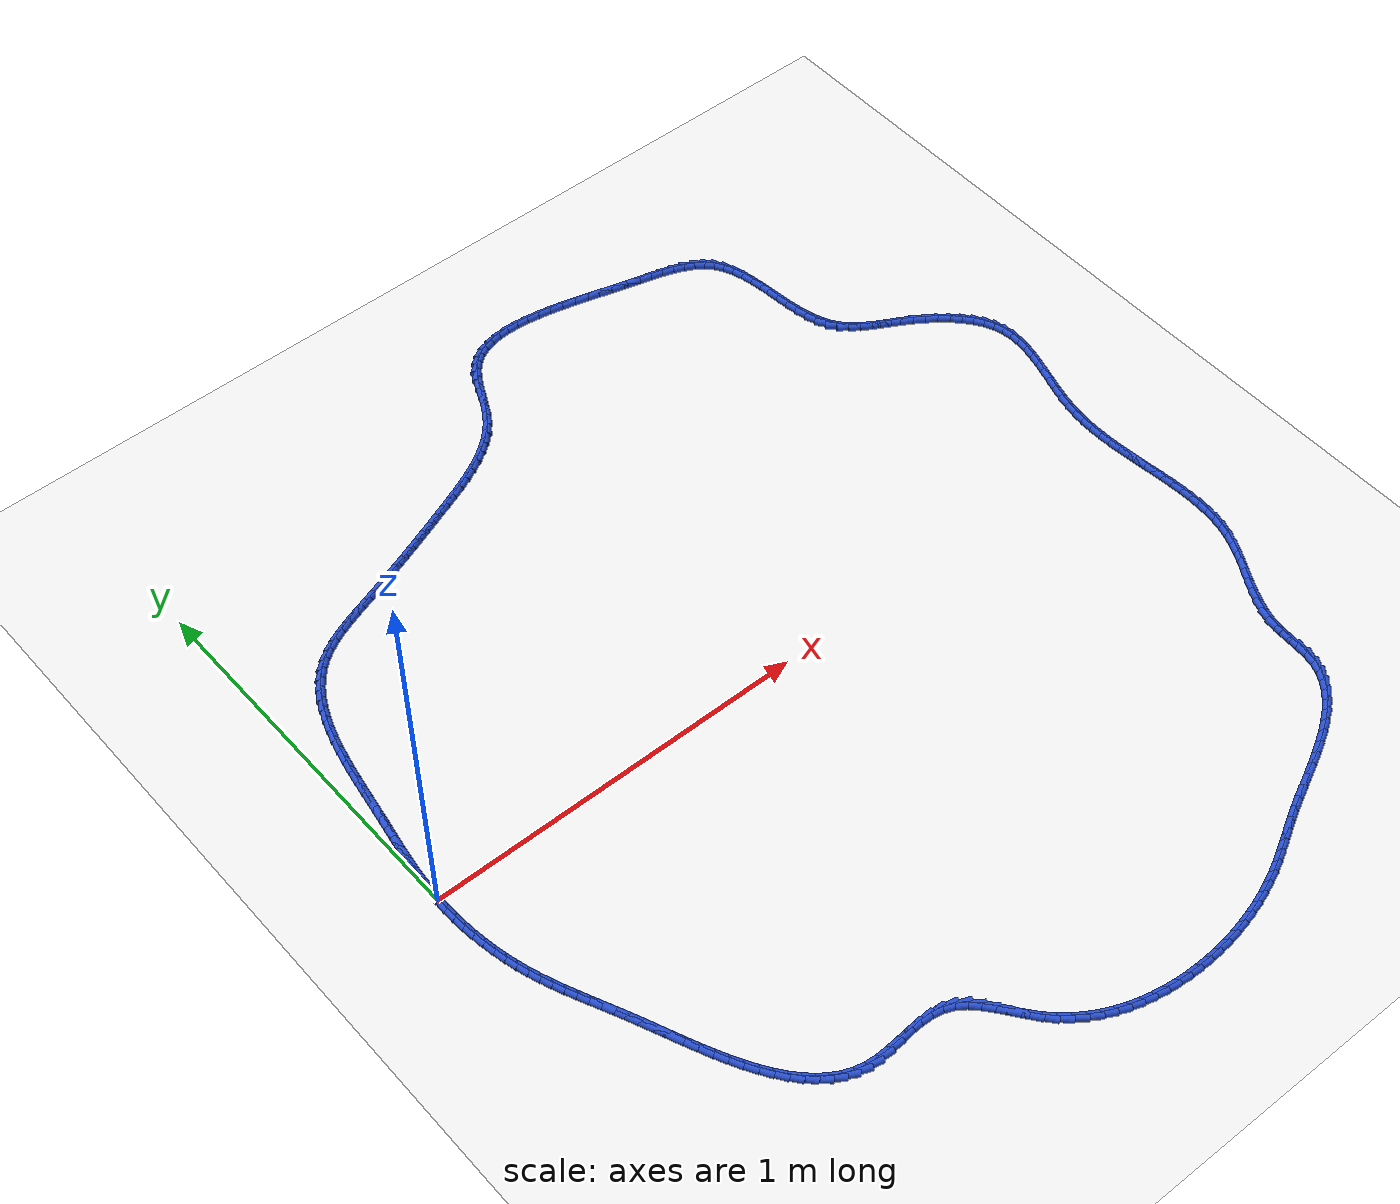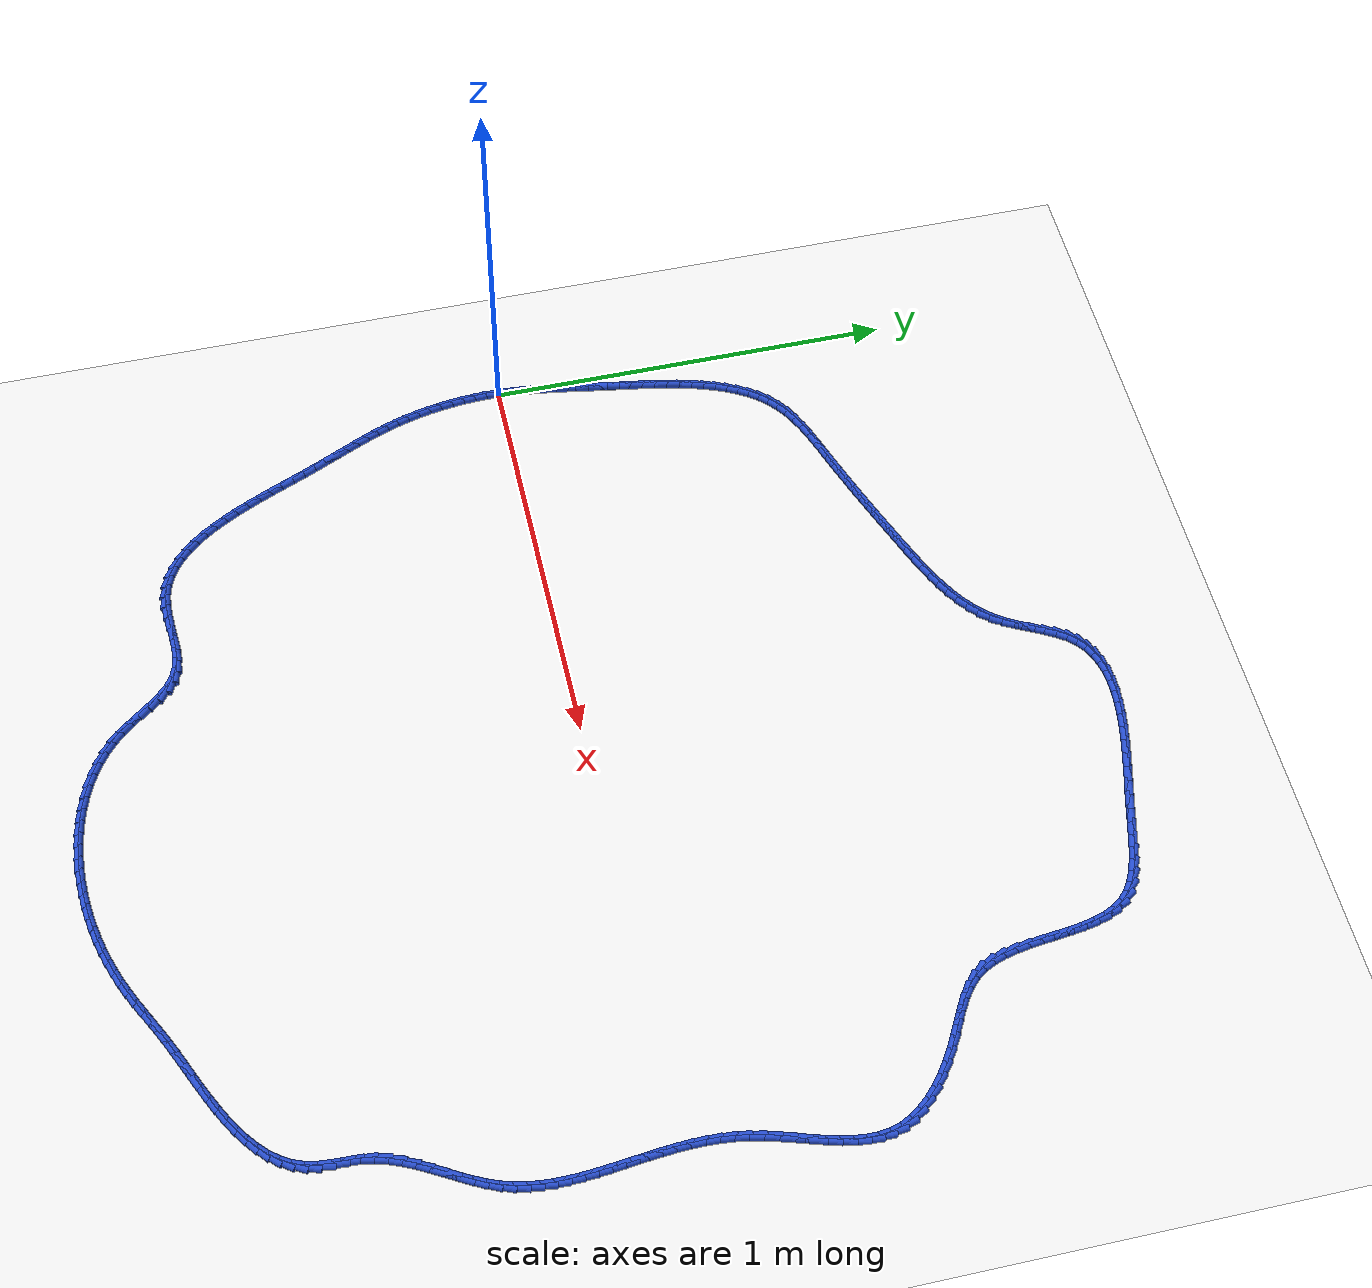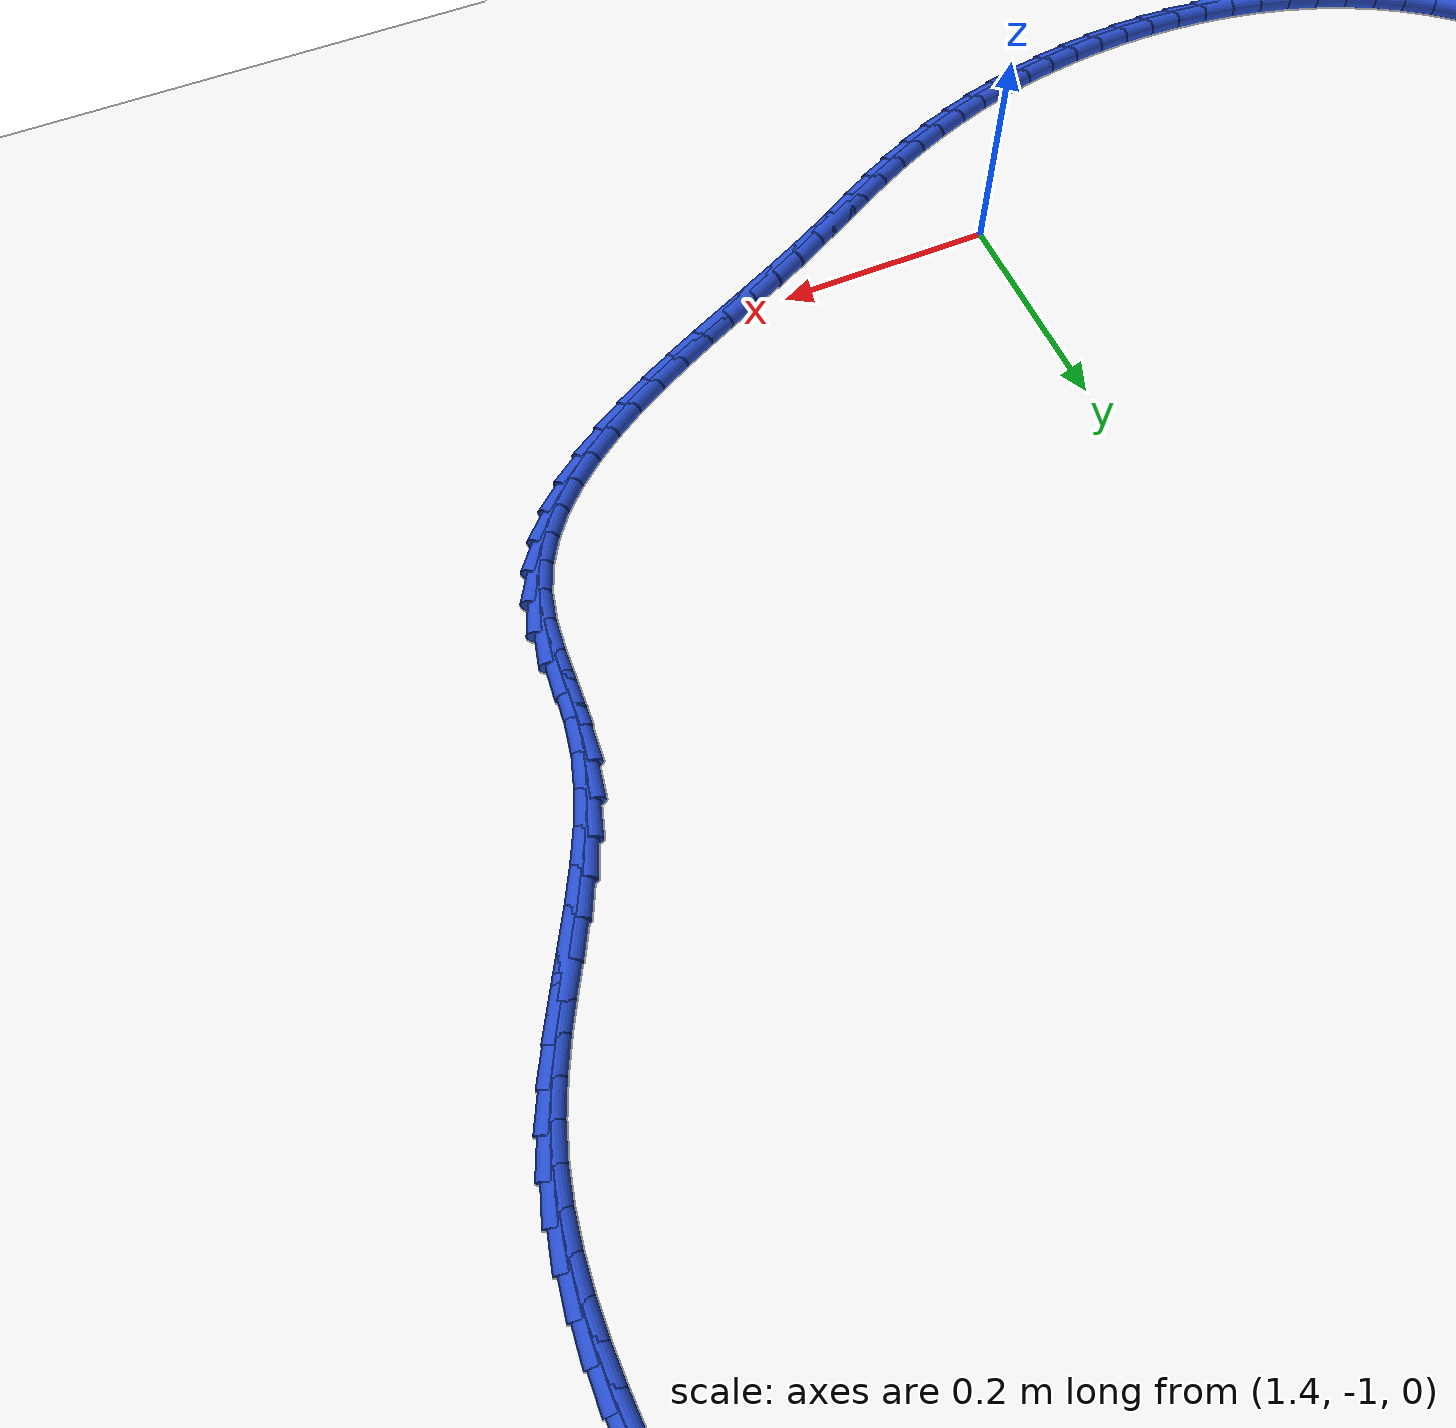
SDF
<sdf version="1.6">
 <world name="default">
  <light name="sun" type="directional">
   <pose>0 0 10 0 -0 0</pose>
   <diffuse>0.8 0.8 0.8 1</diffuse>
   <specular>0.2 0.2 0.2 1</specular>
   <attenuation>
    <range>1000</range>
    <constant>0.9</constant>
    <linear>0.01</linear>
    <quadratic>0.001</quadratic>
   </attenuation>
   <direction>-0.5 0.1 -0.9</direction>
  </light>
  <model name="ground_plane">
   <static>1</static>
   <link name="link">
    <collision name="collision">
     <geometry><plane><normal>0 0 1</normal><size>100 100</size></plane></geometry>
     <surface><friction><ode><mu>100</mu><mu2>50</mu2></ode></friction></surface>
    </collision>
    <visual name="visual">
     <cast_shadows>0</cast_shadows>
     <geometry><plane><normal>0 0 1</normal><size>100 100</size></plane></geometry>
     <material>
      <script><uri>file://media/materials/scripts/gazebo.material</uri><name>Gazebo/WhiteGlow</name></script>
     </material>
    </visual>
   </link>
  </model>
  <gravity>0 0 -9.8</gravity>
  <magnetic_field>6e-06 2.3e-05 -4.2e-05</magnetic_field>
  <atmosphere type="adiabatic"/>
  <physics name="default_physics" default="0" type="ode">
   <max_step_size>0.001</max_step_size>
   <real_time_factor>1</real_time_factor>
   <real_time_update_rate>1000</real_time_update_rate>
  </physics>
  <scene><ambient>0.4 0.4 0.4 1</ambient><background>0.7 0.7 0.7 1</background><shadows>1</shadows></scene>
  <spherical_coordinates>
   <surface_model>EARTH_WGS84</surface_model>
   <latitude_deg>0</latitude_deg>
   <longitude_deg>0</longitude_deg>
   <elevation>0</elevation>
   <heading_deg>0</heading_deg>
  </spherical_coordinates>
  <model name="line">
   <link name="link_0">
    <pose>1.8214596497756474e-17 6.245004513516506e-17 0.01 0 1.57 1.5237638936106588</pose>
    <collision name="collision">
     <geometry><cylinder><radius>0.01</radius><length>0.08</length></cylinder></geometry>
    </collision>
    <visual name="visual">
     <material>
      <script><name>Gazebo/Blue</name><uri>file://media/materials/scripts/gazebo.material</uri></script>
     </material>
     <geometry><cylinder><radius>0.01</radius><length>0.08</length></cylinder></geometry>
    </visual>
   </link>
   <link name="link_1">
    <pose>0.001388095840938239 0.029491822635947733 0.01 0 1.57 1.4903044972762696</pose>
    <collision name="collision">
     <geometry><cylinder><radius>0.01</radius><length>0.08</length></cylinder></geometry>
    </collision>
    <visual name="visual">
     <material>
      <script><name>Gazebo/Blue</name><uri>file://media/materials/scripts/gazebo.material</uri></script>
     </material>
     <geometry><cylinder><radius>0.01</radius><length>0.08</length></cylinder></geometry>
    </visual>
   </link>
   <link name="link_2">
    <pose>0.0037495693808278323 0.05876648822106973 0.01 0 1.57 1.4618585309909409</pose>
    <collision name="collision">
     <geometry><cylinder><radius>0.01</radius><length>0.08</length></cylinder></geometry>
    </collision>
    <visual name="visual">
     <material>
      <script><name>Gazebo/Blue</name><uri>file://media/materials/scripts/gazebo.material</uri></script>
     </material>
     <geometry><cylinder><radius>0.01</radius><length>0.08</length></cylinder></geometry>
    </visual>
   </link>
   <link name="link_3">
    <pose>0.006939304391595864 0.08793090258505902 0.01 0 1.57 1.4387590662165866</pose>
    <collision name="collision">
     <geometry><cylinder><radius>0.01</radius><length>0.08</length></cylinder></geometry>
    </collision>
    <visual name="visual">
     <material>
      <script><name>Gazebo/Blue</name><uri>file://media/materials/scripts/gazebo.material</uri></script>
     </material>
     <geometry><cylinder><radius>0.01</radius><length>0.08</length></cylinder></geometry>
    </visual>
   </link>
   <link name="link_4">
    <pose>0.010812184645169386 0.1170919715576085 0.01 0 1.57 1.4211974750650884</pose>
    <collision name="collision">
     <geometry><cylinder><radius>0.01</radius><length>0.08</length></cylinder></geometry>
    </collision>
    <visual name="visual">
     <material>
      <script><name>Gazebo/Blue</name><uri>file://media/materials/scripts/gazebo.material</uri></script>
     </material>
     <geometry><cylinder><radius>0.01</radius><length>0.08</length></cylinder></geometry>
    </visual>
   </link>
   <link name="link_5">
    <pose>0.015223093913475459 0.14635660096841105 0.01 0 1.57 1.409237766442982</pose>
    <collision name="collision">
     <geometry><cylinder><radius>0.01</radius><length>0.08</length></cylinder></geometry>
    </collision>
    <visual name="visual">
     <material>
      <script><name>Gazebo/Blue</name><uri>file://media/materials/scripts/gazebo.material</uri></script>
     </material>
     <geometry><cylinder><radius>0.01</radius><length>0.08</length></cylinder></geometry>
    </visual>
   </link>
   <link name="link_6">
    <pose>0.02002691596844115 0.17583169664715967 0.01 0 1.57 1.4028335881263194</pose>
    <collision name="collision">
     <geometry><cylinder><radius>0.01</radius><length>0.08</length></cylinder></geometry>
    </collision>
    <visual name="visual">
     <material>
      <script><name>Gazebo/Blue</name><uri>file://media/materials/scripts/gazebo.material</uri></script>
     </material>
     <geometry><cylinder><radius>0.01</radius><length>0.08</length></cylinder></geometry>
    </visual>
   </link>
   <link name="link_7">
    <pose>0.0250785345819935 0.20562416442354708 0.01 0 1.57 1.4018448797821952</pose>
    <collision name="collision">
     <geometry><cylinder><radius>0.01</radius><length>0.08</length></cylinder></geometry>
    </collision>
    <visual name="visual">
     <material>
      <script><name>Gazebo/Blue</name><uri>file://media/materials/scripts/gazebo.material</uri></script>
     </material>
     <geometry><cylinder><radius>0.01</radius><length>0.08</length></cylinder></geometry>
    </visual>
   </link>
   <link name="link_8">
    <pose>0.030232833526059592 0.23584091012726643 0.01 0 1.57 1.40602227225799</pose>
    <collision name="collision">
     <geometry><cylinder><radius>0.01</radius><length>0.08</length></cylinder></geometry>
    </collision>
    <visual name="visual">
     <material>
      <script><name>Gazebo/Blue</name><uri>file://media/materials/scripts/gazebo.material</uri></script>
     </material>
     <geometry><cylinder><radius>0.01</radius><length>0.08</length></cylinder></geometry>
    </visual>
   </link>
   <link name="link_9">
    <pose>0.03534551819406179 0.2665880449480147 0.01 0 1.57 1.4115428015195102</pose>
    <collision name="collision">
     <geometry><cylinder><radius>0.01</radius><length>0.08</length></cylinder></geometry>
    </collision>
    <visual name="visual">
     <material>
      <script><name>Gazebo/Blue</name><uri>file://media/materials/scripts/gazebo.material</uri></script>
     </material>
     <geometry><cylinder><radius>0.01</radius><length>0.08</length></cylinder></geometry>
    </visual>
   </link>
   <link name="link_10">
    <pose>0.04037084859359921 0.29787636192883105 0.01 0 1.57 1.4115779561351656</pose>
    <collision name="collision">
     <geometry><cylinder><radius>0.01</radius><length>0.08</length></cylinder></geometry>
    </collision>
    <visual name="visual">
     <material>
      <script><name>Gazebo/Blue</name><uri>file://media/materials/scripts/gazebo.material</uri></script>
     </material>
     <geometry><cylinder><radius>0.01</radius><length>0.08</length></cylinder></geometry>
    </visual>
   </link>
   <link name="link_11">
    <pose>0.045454030789544374 0.3295319785961077 0.01 0 1.57 1.4055416378496919</pose>
    <collision name="collision">
     <geometry><cylinder><radius>0.01</radius><length>0.08</length></cylinder></geometry>
    </collision>
    <visual name="visual">
     <material>
      <script><name>Gazebo/Blue</name><uri>file://media/materials/scripts/gazebo.material</uri></script>
     </material>
     <geometry><cylinder><radius>0.01</radius><length>0.08</length></cylinder></geometry>
    </visual>
   </link>
   <link name="link_12">
    <pose>0.05076214503595253 0.3613598566207763 0.01 0 1.57 1.3934585145236462</pose>
    <collision name="collision">
     <geometry><cylinder><radius>0.01</radius><length>0.08</length></cylinder></geometry>
    </collision>
    <visual name="visual">
     <material>
      <script><name>Gazebo/Blue</name><uri>file://media/materials/scripts/gazebo.material</uri></script>
     </material>
     <geometry><cylinder><radius>0.01</radius><length>0.08</length></cylinder></geometry>
    </visual>
   </link>
   <link name="link_13">
    <pose>0.056462271586878894 0.39316495767376775 0.01 0 1.57 1.375174199452225</pose>
    <collision name="collision">
     <geometry><cylinder><radius>0.01</radius><length>0.08</length></cylinder></geometry>
    </collision>
    <visual name="visual">
     <material>
      <script><name>Gazebo/Blue</name><uri>file://media/materials/scripts/gazebo.material</uri></script>
     </material>
     <geometry><cylinder><radius>0.01</radius><length>0.08</length></cylinder></geometry>
    </visual>
   </link>
   <link name="link_14">
    <pose>0.06272149069637867 0.4247522434260134 0.01 0 1.57 1.3503630659627126</pose>
    <collision name="collision">
     <geometry><cylinder><radius>0.01</radius><length>0.08</length></cylinder></geometry>
    </collision>
    <visual name="visual">
     <material>
      <script><name>Gazebo/Blue</name><uri>file://media/materials/scripts/gazebo.material</uri></script>
     </material>
     <geometry><cylinder><radius>0.01</radius><length>0.08</length></cylinder></geometry>
    </visual>
   </link>
   <link name="link_15">
    <pose>0.06970688261850713 0.45592667554844485 0.01 0 1.57 1.3185332928578133</pose>
    <collision name="collision">
     <geometry><cylinder><radius>0.01</radius><length>0.08</length></cylinder></geometry>
    </collision>
    <visual name="visual">
     <material>
      <script><name>Gazebo/Blue</name><uri>file://media/materials/scripts/gazebo.material</uri></script>
     </material>
     <geometry><cylinder><radius>0.01</radius><length>0.08</length></cylinder></geometry>
    </visual>
   </link>
   <link name="link_16">
    <pose>0.0775855276073195 0.4864932157119933 0.01 0 1.57 1.2790345468325868</pose>
    <collision name="collision">
     <geometry><cylinder><radius>0.01</radius><length>0.08</length></cylinder></geometry>
    </collision>
    <visual name="visual">
     <material>
      <script><name>Gazebo/Blue</name><uri>file://media/materials/scripts/gazebo.material</uri></script>
     </material>
     <geometry><cylinder><radius>0.01</radius><length>0.08</length></cylinder></geometry>
    </visual>
   </link>
   <link name="link_17">
    <pose>0.08652450591687098 0.5162568255875898 0.01 0 1.57 1.2310767880075248</pose>
    <collision name="collision">
     <geometry><cylinder><radius>0.01</radius><length>0.08</length></cylinder></geometry>
    </collision>
    <visual name="visual">
     <material>
      <script><name>Gazebo/Blue</name><uri>file://media/materials/scripts/gazebo.material</uri></script>
     </material>
     <geometry><cylinder><radius>0.01</radius><length>0.08</length></cylinder></geometry>
    </visual>
   </link>
   <link name="link_18">
    <pose>0.09669089780121684 0.5450224668461662 0.01 0 1.57 1.1737733855634318</pose>
    <collision name="collision">
     <geometry><cylinder><radius>0.01</radius><length>0.08</length></cylinder></geometry>
    </collision>
    <visual name="visual">
     <material>
      <script><name>Gazebo/Blue</name><uri>file://media/materials/scripts/gazebo.material</uri></script>
     </material>
     <geometry><cylinder><radius>0.01</radius><length>0.08</length></cylinder></geometry>
    </visual>
   </link>
   <link name="link_19">
    <pose>0.10825178351441228 0.5725951011586532 0.01 0 1.57 1.1062275232757208</pose>
    <collision name="collision">
     <geometry><cylinder><radius>0.01</radius><length>0.08</length></cylinder></geometry>
    </collision>
    <visual name="visual">
     <material>
      <script><name>Gazebo/Blue</name><uri>file://media/materials/scripts/gazebo.material</uri></script>
     </material>
     <geometry><cylinder><radius>0.01</radius><length>0.08</length></cylinder></geometry>
    </visual>
   </link>
   <link name="link_20">
    <pose>0.12137424331051255 0.5987796901959827 0.01 0 1.57 1.0276849493713263</pose>
    <collision name="collision">
     <geometry><cylinder><radius>0.01</radius><length>0.08</length></cylinder></geometry>
    </collision>
    <visual name="visual">
     <material>
      <script><name>Gazebo/Blue</name><uri>file://media/materials/scripts/gazebo.material</uri></script>
     </material>
     <geometry><cylinder><radius>0.01</radius><length>0.08</length></cylinder></geometry>
    </visual>
   </link>
   <link name="link_21">
    <pose>0.13622535744357284 0.6233811956290853 0.01 0 1.57 0.9377711497290439</pose>
    <collision name="collision">
     <geometry><cylinder><radius>0.01</radius><length>0.08</length></cylinder></geometry>
    </collision>
    <visual name="visual">
     <material>
      <script><name>Gazebo/Blue</name><uri>file://media/materials/scripts/gazebo.material</uri></script>
     </material>
     <geometry><cylinder><radius>0.01</radius><length>0.08</length></cylinder></geometry>
    </visual>
   </link>
   <link name="link_22">
    <pose>0.15297220616764845 0.6462045791288932 0.01 0 1.57 0.8368043085060505</pose>
    <collision name="collision">
     <geometry><cylinder><radius>0.01</radius><length>0.08</length></cylinder></geometry>
    </collision>
    <visual name="visual">
     <material>
      <script><name>Gazebo/Blue</name><uri>file://media/materials/scripts/gazebo.material</uri></script>
     </material>
     <geometry><cylinder><radius>0.01</radius><length>0.08</length></cylinder></geometry>
    </visual>
   </link>
   <link name="link_23">
    <pose>0.17178186973679455 0.667054802366337 0.01 0 1.57 0.726116245392412</pose>
    <collision name="collision">
     <geometry><cylinder><radius>0.01</radius><length>0.08</length></cylinder></geometry>
    </collision>
    <visual name="visual">
     <material>
      <script><name>Gazebo/Blue</name><uri>file://media/materials/scripts/gazebo.material</uri></script>
     </material>
     <geometry><cylinder><radius>0.01</radius><length>0.08</length></cylinder></geometry>
    </visual>
   </link>
   <link name="link_24">
    <pose>0.19282142840506644 0.6857368270123481 0.01 0 1.57 0.611949974813165</pose>
    <collision name="collision">
     <geometry><cylinder><radius>0.01</radius><length>0.08</length></cylinder></geometry>
    </collision>
    <visual name="visual">
     <material>
      <script><name>Gazebo/Blue</name><uri>file://media/materials/scripts/gazebo.material</uri></script>
     </material>
     <geometry><cylinder><radius>0.01</radius><length>0.08</length></cylinder></geometry>
    </visual>
   </link>
   <link name="link_25">
    <pose>0.21617948076257365 0.7021301000594293 0.01 0 1.57 0.5149626203158446</pose>
    <collision name="collision">
     <geometry><cylinder><radius>0.01</radius><length>0.08</length></cylinder></geometry>
    </collision>
    <visual name="visual">
     <material>
      <script><name>Gazebo/Blue</name><uri>file://media/materials/scripts/gazebo.material</uri></script>
     </material>
     <geometry><cylinder><radius>0.01</radius><length>0.08</length></cylinder></geometry>
    </visual>
   </link>
   <link name="link_26">
    <pose>0.24155100281603242 0.7164876475404285 0.01 0 1.57 0.44002951846939714</pose>
    <collision name="collision">
     <geometry><cylinder><radius>0.01</radius><length>0.08</length></cylinder></geometry>
    </collision>
    <visual name="visual">
     <material>
      <script><name>Gazebo/Blue</name><uri>file://media/materials/scripts/gazebo.material</uri></script>
     </material>
     <geometry><cylinder><radius>0.01</radius><length>0.08</length></cylinder></geometry>
    </visual>
   </link>
   <link name="link_27">
    <pose>0.26850782767663767 0.7291793678595357 0.01 0 1.57 0.3851054796450259</pose>
    <collision name="collision">
     <geometry><cylinder><radius>0.01</radius><length>0.08</length></cylinder></geometry>
    </collision>
    <visual name="visual">
     <material>
      <script><name>Gazebo/Blue</name><uri>file://media/materials/scripts/gazebo.material</uri></script>
     </material>
     <geometry><cylinder><radius>0.01</radius><length>0.08</length></cylinder></geometry>
    </visual>
   </link>
   <link name="link_28">
    <pose>0.29662174632080085 0.7405751994101897 0.01 0 1.57 0.34820711535109883</pose>
    <collision name="collision">
     <geometry><cylinder><radius>0.01</radius><length>0.08</length></cylinder></geometry>
    </collision>
    <visual name="visual">
     <material>
      <script><name>Gazebo/Blue</name><uri>file://media/materials/scripts/gazebo.material</uri></script>
     </material>
     <geometry><cylinder><radius>0.01</radius><length>0.08</length></cylinder></geometry>
    </visual>
   </link>
   <link name="link_29">
    <pose>0.32546454972493427 0.7510450805858301 0.01 0 1.57 0.3278949395724656</pose>
    <collision name="collision">
     <geometry><cylinder><radius>0.01</radius><length>0.08</length></cylinder></geometry>
    </collision>
    <visual name="visual">
     <material>
      <script><name>Gazebo/Blue</name><uri>file://media/materials/scripts/gazebo.material</uri></script>
     </material>
     <geometry><cylinder><radius>0.01</radius><length>0.08</length></cylinder></geometry>
    </visual>
   </link>
   <link name="link_30">
    <pose>0.35460802886544934 0.7609589497798951 0.01 0 1.57 0.3233779443561017</pose>
    <collision name="collision">
     <geometry><cylinder><radius>0.01</radius><length>0.08</length></cylinder></geometry>
    </collision>
    <visual name="visual">
     <material>
      <script><name>Gazebo/Blue</name><uri>file://media/materials/scripts/gazebo.material</uri></script>
     </material>
     <geometry><cylinder><radius>0.01</radius><length>0.08</length></cylinder></geometry>
    </visual>
   </link>
   <link name="link_31">
    <pose>0.38362711490932233 0.7706844796199986 0.01 0 1.57 0.3286920556149737</pose>
    <collision name="collision">
     <geometry><cylinder><radius>0.01</radius><length>0.08</length></cylinder></geometry>
    </collision>
    <visual name="visual">
     <material>
      <script><name>Gazebo/Blue</name><uri>file://media/materials/scripts/gazebo.material</uri></script>
     </material>
     <geometry><cylinder><radius>0.01</radius><length>0.08</length></cylinder></geometry>
    </visual>
   </link>
   <link name="link_32">
    <pose>0.4122801526897016 0.7804570028619167 0.01 0 1.57 0.33470451549707375</pose>
    <collision name="collision">
     <geometry><cylinder><radius>0.01</radius><length>0.08</length></cylinder></geometry>
    </collision>
    <visual name="visual">
     <material>
      <script><name>Gazebo/Blue</name><uri>file://media/materials/scripts/gazebo.material</uri></script>
     </material>
     <geometry><cylinder><radius>0.01</radius><length>0.08</length></cylinder></geometry>
    </visual>
   </link>
   <link name="link_33">
    <pose>0.440606941147344 0.7903087725165727 0.01 0 1.57 0.340591693265679</pose>
    <collision name="collision">
     <geometry><cylinder><radius>0.01</radius><length>0.08</length></cylinder></geometry>
    </collision>
    <visual name="visual">
     <material>
      <script><name>Gazebo/Blue</name><uri>file://media/materials/scripts/gazebo.material</uri></script>
     </material>
     <geometry><cylinder><radius>0.01</radius><length>0.08</length></cylinder></geometry>
    </visual>
   </link>
   <link name="link_34">
    <pose>0.46867116174943524 0.8002548094520903 0.01 0 1.57 0.3463116413430221</pose>
    <collision name="collision">
     <geometry><cylinder><radius>0.01</radius><length>0.08</length></cylinder></geometry>
    </collision>
    <visual name="visual">
     <material>
      <script><name>Gazebo/Blue</name><uri>file://media/materials/scripts/gazebo.material</uri></script>
     </material>
     <geometry><cylinder><radius>0.01</radius><length>0.08</length></cylinder></geometry>
    </visual>
   </link>
   <link name="link_35">
    <pose>0.49653649596316135 0.8103101345365932 0.01 0 1.57 0.35182365664351933</pose>
    <collision name="collision">
     <geometry><cylinder><radius>0.01</radius><length>0.08</length></cylinder></geometry>
    </collision>
    <visual name="visual">
     <material>
      <script><name>Gazebo/Blue</name><uri>file://media/materials/scripts/gazebo.material</uri></script>
     </material>
     <geometry><cylinder><radius>0.01</radius><length>0.08</length></cylinder></geometry>
    </visual>
   </link>
   <link name="link_36">
    <pose>0.524266625255708 0.8204897686382059 0.01 0 1.57 0.35708921926782794</pose>
    <collision name="collision">
     <geometry><cylinder><radius>0.01</radius><length>0.08</length></cylinder></geometry>
    </collision>
    <visual name="visual">
     <material>
      <script><name>Gazebo/Blue</name><uri>file://media/materials/scripts/gazebo.material</uri></script>
     </material>
     <geometry><cylinder><radius>0.01</radius><length>0.08</length></cylinder></geometry>
    </visual>
   </link>
   <link name="link_37">
    <pose>0.5519252310942612 0.830808732625052 0.01 0 1.57 0.36207287650573394</pose>
    <collision name="collision">
     <geometry><cylinder><radius>0.01</radius><length>0.08</length></cylinder></geometry>
    </collision>
    <visual name="visual">
     <material>
      <script><name>Gazebo/Blue</name><uri>file://media/materials/scripts/gazebo.material</uri></script>
     </material>
     <geometry><cylinder><radius>0.01</radius><length>0.08</length></cylinder></geometry>
    </visual>
   </link>
   <link name="link_38">
    <pose>0.5795759949460065 0.8412820473652557 0.01 0 1.57 0.36674303009309084</pose>
    <collision name="collision">
     <geometry><cylinder><radius>0.01</radius><length>0.08</length></cylinder></geometry>
    </collision>
    <visual name="visual">
     <material>
      <script><name>Gazebo/Blue</name><uri>file://media/materials/scripts/gazebo.material</uri></script>
     </material>
     <geometry><cylinder><radius>0.01</radius><length>0.08</length></cylinder></geometry>
    </visual>
   </link>
   <link name="link_39">
    <pose>0.6072825982781304 0.8519247337269412 0.01 0 1.57 0.371072590450601</pose>
    <collision name="collision">
     <geometry><cylinder><radius>0.01</radius><length>0.08</length></cylinder></geometry>
    </collision>
    <visual name="visual">
     <material>
      <script><name>Gazebo/Blue</name><uri>file://media/materials/scripts/gazebo.material</uri></script>
     </material>
     <geometry><cylinder><radius>0.01</radius><length>0.08</length></cylinder></geometry>
    </visual>
   </link>
   <link name="link_40">
    <pose>0.6351087225578178 0.8627518125782321 0.01 0 1.57 0.3750394702391534</pose>
    <collision name="collision">
     <geometry><cylinder><radius>0.01</radius><length>0.08</length></cylinder></geometry>
    </collision>
    <visual name="visual">
     <material>
      <script><name>Gazebo/Blue</name><uri>file://media/materials/scripts/gazebo.material</uri></script>
     </material>
     <geometry><cylinder><radius>0.01</radius><length>0.08</length></cylinder></geometry>
    </visual>
   </link>
   <link name="link_41">
    <pose>0.6631180492522555 0.8737783047872529 0.01 0 1.57 0.3788108036732851</pose>
    <collision name="collision">
     <geometry><cylinder><radius>0.01</radius><length>0.08</length></cylinder></geometry>
    </collision>
    <visual name="visual">
     <material>
      <script><name>Gazebo/Blue</name><uri>file://media/materials/scripts/gazebo.material</uri></script>
     </material>
     <geometry><cylinder><radius>0.01</radius><length>0.08</length></cylinder></geometry>
    </visual>
   </link>
   <link name="link_42">
    <pose>0.6913684645730679 0.8850229437640316 0.01 0 1.57 0.38735656196633544</pose>
    <collision name="collision">
     <geometry><cylinder><radius>0.01</radius><length>0.08</length></cylinder></geometry>
    </collision>
    <visual name="visual">
     <material>
      <script><name>Gazebo/Blue</name><uri>file://media/materials/scripts/gazebo.material</uri></script>
     </material>
     <geometry><cylinder><radius>0.01</radius><length>0.08</length></cylinder></geometry>
    </visual>
   </link>
   <link name="link_43">
    <pose>0.7197598100594127 0.896605709095443 0.01 0 1.57 0.40611140686019187</pose>
    <collision name="collision">
     <geometry><cylinder><radius>0.01</radius><length>0.08</length></cylinder></geometry>
    </collision>
    <visual name="visual">
     <material>
      <script><name>Gazebo/Blue</name><uri>file://media/materials/scripts/gazebo.material</uri></script>
     </material>
     <geometry><cylinder><radius>0.01</radius><length>0.08</length></cylinder></geometry>
    </visual>
   </link>
   <link name="link_44">
    <pose>0.7480187691509006 0.9087575084704903 0.01 0 1.57 0.435545099000935</pose>
    <collision name="collision">
     <geometry><cylinder><radius>0.01</radius><length>0.08</length></cylinder></geometry>
    </collision>
    <visual name="visual">
     <material>
      <script><name>Gazebo/Blue</name><uri>file://media/materials/scripts/gazebo.material</uri></script>
     </material>
     <geometry><cylinder><radius>0.01</radius><length>0.08</length></cylinder></geometry>
    </visual>
   </link>
   <link name="link_45">
    <pose>0.7758631994407497 0.9217149035694885 0.01 0 1.57 0.47611266428190374</pose>
    <collision name="collision">
     <geometry><cylinder><radius>0.01</radius><length>0.08</length></cylinder></geometry>
    </collision>
    <visual name="visual">
     <material>
      <script><name>Gazebo/Blue</name><uri>file://media/materials/scripts/gazebo.material</uri></script>
     </material>
     <geometry><cylinder><radius>0.01</radius><length>0.08</length></cylinder></geometry>
    </visual>
   </link>
   <link name="link_46">
    <pose>0.8030109585221777 0.9357144560727523 0.01 0 1.57 0.5284465386728658</pose>
    <collision name="collision">
     <geometry><cylinder><radius>0.01</radius><length>0.08</length></cylinder></geometry>
    </collision>
    <visual name="visual">
     <material>
      <script><name>Gazebo/Blue</name><uri>file://media/materials/scripts/gazebo.material</uri></script>
     </material>
     <geometry><cylinder><radius>0.01</radius><length>0.08</length></cylinder></geometry>
    </visual>
   </link>
   <link name="link_47">
    <pose>0.8291799039884026 0.950992727660596 0.01 0 1.57 0.5932160414529968</pose>
    <collision name="collision">
     <geometry><cylinder><radius>0.01</radius><length>0.08</length></cylinder></geometry>
    </collision>
    <visual name="visual">
     <material>
      <script><name>Gazebo/Blue</name><uri>file://media/materials/scripts/gazebo.material</uri></script>
     </material>
     <geometry><cylinder><radius>0.01</radius><length>0.08</length></cylinder></geometry>
    </visual>
   </link>
   <link name="link_48">
    <pose>0.8540878934326424 0.9677862800133346 0.01 0 1.57 0.6709055320872783</pose>
    <collision name="collision">
     <geometry><cylinder><radius>0.01</radius><length>0.08</length></cylinder></geometry>
    </collision>
    <visual name="visual">
     <material>
      <script><name>Gazebo/Blue</name><uri>file://media/materials/scripts/gazebo.material</uri></script>
     </material>
     <geometry><cylinder><radius>0.01</radius><length>0.08</length></cylinder></geometry>
    </visual>
   </link>
   <link name="link_49">
    <pose>0.8774527844481144 0.9863316748112816 0.01 0 1.57 0.7614956853872528</pose>
    <collision name="collision">
     <geometry><cylinder><radius>0.01</radius><length>0.08</length></cylinder></geometry>
    </collision>
    <visual name="visual">
     <material>
      <script><name>Gazebo/Blue</name><uri>file://media/materials/scripts/gazebo.material</uri></script>
     </material>
     <geometry><cylinder><radius>0.01</radius><length>0.08</length></cylinder></geometry>
    </visual>
   </link>
   <link name="link_50">
    <pose>0.8989924346280368 1.0068654737347524 0.01 0 1.57 0.8640791148845518</pose>
    <collision name="collision">
     <geometry><cylinder><radius>0.01</radius><length>0.08</length></cylinder></geometry>
    </collision>
    <visual name="visual">
     <material>
      <script><name>Gazebo/Blue</name><uri>file://media/materials/scripts/gazebo.material</uri></script>
     </material>
     <geometry><cylinder><radius>0.01</radius><length>0.08</length></cylinder></geometry>
    </visual>
   </link>
   <link name="link_51">
    <pose>0.9184247015656273 1.029624238464061 0.01 0 1.57 0.9747205344733441</pose>
    <collision name="collision">
     <geometry><cylinder><radius>0.01</radius><length>0.08</length></cylinder></geometry>
    </collision>
    <visual name="visual">
     <material>
      <script><name>Gazebo/Blue</name><uri>file://media/materials/scripts/gazebo.material</uri></script>
     </material>
     <geometry><cylinder><radius>0.01</radius><length>0.08</length></cylinder></geometry>
    </visual>
   </link>
   <link name="link_52">
    <pose>0.9355039355843339 1.0548003191148174 0.01 0 1.57 1.0624680241747346</pose>
    <collision name="collision">
     <geometry><cylinder><radius>0.01</radius><length>0.08</length></cylinder></geometry>
    </collision>
    <visual name="visual">
     <material>
      <script><name>Gazebo/Blue</name><uri>file://media/materials/scripts/gazebo.material</uri></script>
     </material>
     <geometry><cylinder><radius>0.01</radius><length>0.08</length></cylinder></geometry>
    </visual>
   </link>
   <link name="link_53">
    <pose>0.9505819275423012 1.0818622564112694 0.01 0 1.57 1.107047828063826</pose>
    <collision name="collision">
     <geometry><cylinder><radius>0.01</radius><length>0.08</length></cylinder></geometry>
    </collision>
    <visual name="visual">
     <material>
      <script><name>Gazebo/Blue</name><uri>file://media/materials/scripts/gazebo.material</uri></script>
     </material>
     <geometry><cylinder><radius>0.01</radius><length>0.08</length></cylinder></geometry>
    </visual>
   </link>
   <link name="link_54">
    <pose>0.9644981729396145 1.1096877285908624 0.01 0 1.57 1.1105482751179812</pose>
    <collision name="collision">
     <geometry><cylinder><radius>0.01</radius><length>0.08</length></cylinder></geometry>
    </collision>
    <visual name="visual">
     <material>
      <script><name>Gazebo/Blue</name><uri>file://media/materials/scripts/gazebo.material</uri></script>
     </material>
     <geometry><cylinder><radius>0.01</radius><length>0.08</length></cylinder></geometry>
    </visual>
   </link>
   <link name="link_55">
    <pose>0.9781064290777485 1.1371371354755604 0.01 0 1.57 1.0712015805934152</pose>
    <collision name="collision">
     <geometry><cylinder><radius>0.01</radius><length>0.08</length></cylinder></geometry>
    </collision>
    <visual name="visual">
     <material>
      <script><name>Gazebo/Blue</name><uri>file://media/materials/scripts/gazebo.material</uri></script>
     </material>
     <geometry><cylinder><radius>0.01</radius><length>0.08</length></cylinder></geometry>
    </visual>
   </link>
   <link name="link_56">
    <pose>0.9922604532581784 1.163070876887328 0.01 0 1.57 0.9817664355590748</pose>
    <collision name="collision">
     <geometry><cylinder><radius>0.01</radius><length>0.08</length></cylinder></geometry>
    </collision>
    <visual name="visual">
     <material>
      <script><name>Gazebo/Blue</name><uri>file://media/materials/scripts/gazebo.material</uri></script>
     </material>
     <geometry><cylinder><radius>0.01</radius><length>0.08</length></cylinder></geometry>
    </visual>
   </link>
   <link name="link_57">
    <pose>1.007814002782379 1.1863493526481295 0.01 0 1.57 0.8328420207081312</pose>
    <collision name="collision">
     <geometry><cylinder><radius>0.01</radius><length>0.08</length></cylinder></geometry>
    </collision>
    <visual name="visual">
     <material>
      <script><name>Gazebo/Blue</name><uri>file://media/materials/scripts/gazebo.material</uri></script>
     </material>
     <geometry><cylinder><radius>0.01</radius><length>0.08</length></cylinder></geometry>
    </visual>
   </link>
   <link name="link_58">
    <pose>1.0255810537056407 1.2058876419827318 0.01 0 1.57 0.6538998330026936</pose>
    <collision name="collision">
     <geometry><cylinder><radius>0.01</radius><length>0.08</length></cylinder></geometry>
    </collision>
    <visual name="visual">
     <material>
      <script><name>Gazebo/Blue</name><uri>file://media/materials/scripts/gazebo.material</uri></script>
     </material>
     <geometry><cylinder><radius>0.01</radius><length>0.08</length></cylinder></geometry>
    </visual>
   </link>
   <link name="link_59">
    <pose>1.0458042035454191 1.221386185064083 0.01 0 1.57 0.481289551205289</pose>
    <collision name="collision">
     <geometry><cylinder><radius>0.01</radius><length>0.08</length></cylinder></geometry>
    </collision>
    <visual name="visual">
     <material>
      <script><name>Gazebo/Blue</name><uri>file://media/materials/scripts/gazebo.material</uri></script>
     </material>
     <geometry><cylinder><radius>0.01</radius><length>0.08</length></cylinder></geometry>
    </visual>
   </link>
   <link name="link_60">
    <pose>1.0682980972082632 1.2331336437885976 0.01 0 1.57 0.3257602040646511</pose>
    <collision name="collision">
     <geometry><cylinder><radius>0.01</radius><length>0.08</length></cylinder></geometry>
    </collision>
    <visual name="visual">
     <material>
      <script><name>Gazebo/Blue</name><uri>file://media/materials/scripts/gazebo.material</uri></script>
     </material>
     <geometry><cylinder><radius>0.01</radius><length>0.08</length></cylinder></geometry>
    </visual>
   </link>
   <link name="link_61">
    <pose>1.0928670368824889 1.241432896139681 0.01 0 1.57 0.19245607330047745</pose>
    <collision name="collision">
     <geometry><cylinder><radius>0.01</radius><length>0.08</length></cylinder></geometry>
    </collision>
    <visual name="visual">
     <material>
      <script><name>Gazebo/Blue</name><uri>file://media/materials/scripts/gazebo.material</uri></script>
     </material>
     <geometry><cylinder><radius>0.01</radius><length>0.08</length></cylinder></geometry>
    </visual>
   </link>
   <link name="link_62">
    <pose>1.119315324756412 1.2465868201007393 0.01 0 1.57 0.0819812979620027</pose>
    <collision name="collision">
     <geometry><cylinder><radius>0.01</radius><length>0.08</length></cylinder></geometry>
    </collision>
    <visual name="visual">
     <material>
      <script><name>Gazebo/Blue</name><uri>file://media/materials/scripts/gazebo.material</uri></script>
     </material>
     <geometry><cylinder><radius>0.01</radius><length>0.08</length></cylinder></geometry>
    </visual>
   </link>
   <link name="link_63">
    <pose>1.1474472630183485 1.2488982936551765 0.01 0 1.57 -0.007700715751210329</pose>
    <collision name="collision">
     <geometry><cylinder><radius>0.01</radius><length>0.08</length></cylinder></geometry>
    </collision>
    <visual name="visual">
     <material>
      <script><name>Gazebo/Blue</name><uri>file://media/materials/scripts/gazebo.material</uri></script>
     </material>
     <geometry><cylinder><radius>0.01</radius><length>0.08</length></cylinder></geometry>
    </visual>
   </link>
   <link name="link_64">
    <pose>1.1770671538566142 1.2486701947863992 0.01 0 1.57 -0.07956709545704521</pose>
    <collision name="collision">
     <geometry><cylinder><radius>0.01</radius><length>0.08</length></cylinder></geometry>
    </collision>
    <visual name="visual">
     <material>
      <script><name>Gazebo/Blue</name><uri>file://media/materials/scripts/gazebo.material</uri></script>
     </material>
     <geometry><cylinder><radius>0.01</radius><length>0.08</length></cylinder></geometry>
    </visual>
   </link>
   <link name="link_65">
    <pose>1.2079792994595255 1.2462054014778121 0.01 0 1.57 -0.13656384455430579</pose>
    <collision name="collision">
     <geometry><cylinder><radius>0.01</radius><length>0.08</length></cylinder></geometry>
    </collision>
    <visual name="visual">
     <material>
      <script><name>Gazebo/Blue</name><uri>file://media/materials/scripts/gazebo.material</uri></script>
     </material>
     <geometry><cylinder><radius>0.01</radius><length>0.08</length></cylinder></geometry>
    </visual>
   </link>
   <link name="link_66">
    <pose>1.2399880020153982 1.2418067917128204 0.01 0 1.57 -0.18120595964699635</pose>
    <collision name="collision">
     <geometry><cylinder><radius>0.01</radius><length>0.08</length></cylinder></geometry>
    </collision>
    <visual name="visual">
     <material>
      <script><name>Gazebo/Blue</name><uri>file://media/materials/scripts/gazebo.material</uri></script>
     </material>
     <geometry><cylinder><radius>0.01</radius><length>0.08</length></cylinder></geometry>
    </visual>
   </link>
   <link name="link_67">
    <pose>1.272897563712548 1.2357772434748293 0.01 0 1.57 -0.215482275003066</pose>
    <collision name="collision">
     <geometry><cylinder><radius>0.01</radius><length>0.08</length></cylinder></geometry>
    </collision>
    <visual name="visual">
     <material>
      <script><name>Gazebo/Blue</name><uri>file://media/materials/scripts/gazebo.material</uri></script>
     </material>
     <geometry><cylinder><radius>0.01</radius><length>0.08</length></cylinder></geometry>
    </visual>
   </link>
   <link name="link_68">
    <pose>1.3065122867392907 1.2284196347472447 0.01 0 1.57 -0.24088548124423756</pose>
    <collision name="collision">
     <geometry><cylinder><radius>0.01</radius><length>0.08</length></cylinder></geometry>
    </collision>
    <visual name="visual">
     <material>
      <script><name>Gazebo/Blue</name><uri>file://media/materials/scripts/gazebo.material</uri></script>
     </material>
     <geometry><cylinder><radius>0.01</radius><length>0.08</length></cylinder></geometry>
    </visual>
   </link>
   <link name="link_69">
    <pose>1.3406364732839424 1.2200368435134714 0.01 0 1.57 -0.25847690739245877</pose>
    <collision name="collision">
     <geometry><cylinder><radius>0.01</radius><length>0.08</length></cylinder></geometry>
    </collision>
    <visual name="visual">
     <material>
      <script><name>Gazebo/Blue</name><uri>file://media/materials/scripts/gazebo.material</uri></script>
     </material>
     <geometry><cylinder><radius>0.01</radius><length>0.08</length></cylinder></geometry>
    </visual>
   </link>
   <link name="link_70">
    <pose>1.3750744255348197 1.2109317477569148 0.01 0 1.57 -0.26894769308820193</pose>
    <collision name="collision">
     <geometry><cylinder><radius>0.01</radius><length>0.08</length></cylinder></geometry>
    </collision>
    <visual name="visual">
     <material>
      <script><name>Gazebo/Blue</name><uri>file://media/materials/scripts/gazebo.material</uri></script>
     </material>
     <geometry><cylinder><radius>0.01</radius><length>0.08</length></cylinder></geometry>
    </visual>
   </link>
   <link name="link_71">
    <pose>1.4096304456802375 1.2014072254609802 0.01 0 1.57 -0.2726623033455674</pose>
    <collision name="collision">
     <geometry><cylinder><radius>0.01</radius><length>0.08</length></cylinder></geometry>
    </collision>
    <visual name="visual">
     <material>
      <script><name>Gazebo/Blue</name><uri>file://media/materials/scripts/gazebo.material</uri></script>
     </material>
     <geometry><cylinder><radius>0.01</radius><length>0.08</length></cylinder></geometry>
    </visual>
   </link>
   <link name="link_72">
    <pose>1.4441088359085128 1.1917661546090736 0.01 0 1.57 -0.26967986547503003</pose>
    <collision name="collision">
     <geometry><cylinder><radius>0.01</radius><length>0.08</length></cylinder></geometry>
    </collision>
    <visual name="visual">
     <material>
      <script><name>Gazebo/Blue</name><uri>file://media/materials/scripts/gazebo.material</uri></script>
     </material>
     <geometry><cylinder><radius>0.01</radius><length>0.08</length></cylinder></geometry>
    </visual>
   </link>
   <link name="link_73">
    <pose>1.4783138984079602 1.1823114131845993 0.01 0 1.57 -0.26067462918415657</pose>
    <collision name="collision">
     <geometry><cylinder><radius>0.01</radius><length>0.08</length></cylinder></geometry>
    </collision>
    <visual name="visual">
     <material>
      <script><name>Gazebo/Blue</name><uri>file://media/materials/scripts/gazebo.material</uri></script>
     </material>
     <geometry><cylinder><radius>0.01</radius><length>0.08</length></cylinder></geometry>
    </visual>
   </link>
   <link name="link_74">
    <pose>1.512040262264226 1.1733151065514773 0.01 0 1.57 -0.2594281349938894</pose>
    <collision name="collision">
     <geometry><cylinder><radius>0.01</radius><length>0.08</length></cylinder></geometry>
    </collision>
    <visual name="visual">
     <material>
      <script><name>Gazebo/Blue</name><uri>file://media/materials/scripts/gazebo.material</uri></script>
     </material>
     <geometry><cylinder><radius>0.01</radius><length>0.08</length></cylinder></geometry>
    </visual>
   </link>
   <link name="link_75">
    <pose>1.5449363382225323 1.1645841820468465 0.01 0 1.57 -0.2780151432640949</pose>
    <collision name="collision">
     <geometry><cylinder><radius>0.01</radius><length>0.08</length></cylinder></geometry>
    </collision>
    <visual name="visual">
     <material>
      <script><name>Gazebo/Blue</name><uri>file://media/materials/scripts/gazebo.material</uri></script>
     </material>
     <geometry><cylinder><radius>0.01</radius><length>0.08</length></cylinder></geometry>
    </visual>
   </link>
   <link name="link_76">
    <pose>1.5765372160493627 1.1555650839224394 0.01 0 1.57 -0.31946563337393913</pose>
    <collision name="collision">
     <geometry><cylinder><radius>0.01</radius><length>0.08</length></cylinder></geometry>
    </collision>
    <visual name="visual">
     <material>
      <script><name>Gazebo/Blue</name><uri>file://media/materials/scripts/gazebo.material</uri></script>
     </material>
     <geometry><cylinder><radius>0.01</radius><length>0.08</length></cylinder></geometry>
    </visual>
   </link>
   <link name="link_77">
    <pose>1.6063750261570189 1.1456948419656532 0.01 0 1.57 -0.3880280987081178</pose>
    <collision name="collision">
     <geometry><cylinder><radius>0.01</radius><length>0.08</length></cylinder></geometry>
    </collision>
    <visual name="visual">
     <material>
      <script><name>Gazebo/Blue</name><uri>file://media/materials/scripts/gazebo.material</uri></script>
     </material>
     <geometry><cylinder><radius>0.01</radius><length>0.08</length></cylinder></geometry>
    </visual>
   </link>
   <link name="link_78">
    <pose>1.6339818989578039 1.1344104859638846 0.01 0 1.57 -0.48924247455947545</pose>
    <collision name="collision">
     <geometry><cylinder><radius>0.01</radius><length>0.08</length></cylinder></geometry>
    </collision>
    <visual name="visual">
     <material>
      <script><name>Gazebo/Blue</name><uri>file://media/materials/scripts/gazebo.material</uri></script>
     </material>
     <geometry><cylinder><radius>0.01</radius><length>0.08</length></cylinder></geometry>
    </visual>
   </link>
   <link name="link_79">
    <pose>1.6588899648640187 1.1211490457045312 0.01 0 1.57 -0.6284826003138324</pose>
    <collision name="collision">
     <geometry><cylinder><radius>0.01</radius><length>0.08</length></cylinder></geometry>
    </collision>
    <visual name="visual">
     <material>
      <script><name>Gazebo/Blue</name><uri>file://media/materials/scripts/gazebo.material</uri></script>
     </material>
     <geometry><cylinder><radius>0.01</radius><length>0.08</length></cylinder></geometry>
    </visual>
   </link>
   <link name="link_80">
    <pose>1.6806313542879658 1.1053475509749897 0.01 0 1.57 -0.8069461461199458</pose>
    <collision name="collision">
     <geometry><cylinder><radius>0.01</radius><length>0.08</length></cylinder></geometry>
    </collision>
    <visual name="visual">
     <material>
      <script><name>Gazebo/Blue</name><uri>file://media/materials/scripts/gazebo.material</uri></script>
     </material>
     <geometry><cylinder><radius>0.01</radius><length>0.08</length></cylinder></geometry>
    </visual>
   </link>
   <link name="link_81">
    <pose>1.698738213850775 1.0864430477496767 0.01 0 1.57 -1.0044543709158333</pose>
    <collision name="collision">
     <geometry><cylinder><radius>0.01</radius><length>0.08</length></cylinder></geometry>
    </collision>
    <visual name="visual">
     <material>
      <script><name>Gazebo/Blue</name><uri>file://media/materials/scripts/gazebo.material</uri></script>
     </material>
     <geometry><cylinder><radius>0.01</radius><length>0.08</length></cylinder></geometry>
    </visual>
   </link>
   <link name="link_82">
    <pose>1.7129544807824657 1.0640840876634172 0.01 0 1.57 -1.1687164294492152</pose>
    <collision name="collision">
     <geometry><cylinder><radius>0.01</radius><length>0.08</length></cylinder></geometry>
    </collision>
    <visual name="visual">
     <material>
      <script><name>Gazebo/Blue</name><uri>file://media/materials/scripts/gazebo.material</uri></script>
     </material>
     <geometry><cylinder><radius>0.01</radius><length>0.08</length></cylinder></geometry>
    </visual>
   </link>
   <link name="link_83">
    <pose>1.723765960297825 1.0386600922077092 0.01 0 1.57 -1.2900923517861294</pose>
    <collision name="collision">
     <geometry><cylinder><radius>0.01</radius><length>0.08</length></cylinder></geometry>
    </collision>
    <visual name="visual">
     <material>
      <script><name>Gazebo/Blue</name><uri>file://media/materials/scripts/gazebo.material</uri></script>
     </material>
     <geometry><cylinder><radius>0.01</radius><length>0.08</length></cylinder></geometry>
    </visual>
   </link>
   <link name="link_84">
    <pose>1.731820802259592 1.010722609099377 0.01 0 1.57 -1.3744793045323496</pose>
    <collision name="collision">
     <geometry><cylinder><radius>0.01</radius><length>0.08</length></cylinder></geometry>
    </collision>
    <visual name="visual">
     <material>
      <script><name>Gazebo/Blue</name><uri>file://media/materials/scripts/gazebo.material</uri></script>
     </material>
     <geometry><cylinder><radius>0.01</radius><length>0.08</length></cylinder></geometry>
    </visual>
   </link>
   <link name="link_85">
    <pose>1.7377671565305066 0.9808231860552452 0.01 0 1.57 -1.4284865832481108</pose>
    <collision name="collision">
     <geometry><cylinder><radius>0.01</radius><length>0.08</length></cylinder></geometry>
    </collision>
    <visual name="visual">
     <material>
      <script><name>Gazebo/Blue</name><uri>file://media/materials/scripts/gazebo.material</uri></script>
     </material>
     <geometry><cylinder><radius>0.01</radius><length>0.08</length></cylinder></geometry>
    </visual>
   </link>
   <link name="link_86">
    <pose>1.7422531729733082 0.9495133707921389 0.01 0 1.57 -1.4570837887705788</pose>
    <collision name="collision">
     <geometry><cylinder><radius>0.01</radius><length>0.08</length></cylinder></geometry>
    </collision>
    <visual name="visual">
     <material>
      <script><name>Gazebo/Blue</name><uri>file://media/materials/scripts/gazebo.material</uri></script>
     </material>
     <geometry><cylinder><radius>0.01</radius><length>0.08</length></cylinder></geometry>
    </visual>
   </link>
   <link name="link_87">
    <pose>1.7459270014507355 0.9173447110268822 0.01 0 1.57 -1.4631406618192042</pose>
    <collision name="collision">
     <geometry><cylinder><radius>0.01</radius><length>0.08</length></cylinder></geometry>
    </collision>
    <visual name="visual">
     <material>
      <script><name>Gazebo/Blue</name><uri>file://media/materials/scripts/gazebo.material</uri></script>
     </material>
     <geometry><cylinder><radius>0.01</radius><length>0.08</length></cylinder></geometry>
    </visual>
   </link>
   <link name="link_88">
    <pose>1.749436791825529 0.8848687544763 0.01 0 1.57 -1.4475125220901743</pose>
    <collision name="collision">
     <geometry><cylinder><radius>0.01</radius><length>0.08</length></cylinder></geometry>
    </collision>
    <visual name="visual">
     <material>
      <script><name>Gazebo/Blue</name><uri>file://media/materials/scripts/gazebo.material</uri></script>
     </material>
     <geometry><cylinder><radius>0.01</radius><length>0.08</length></cylinder></geometry>
    </visual>
   </link>
   <link name="link_89">
    <pose>1.7534306939604287 0.8526370488572165 0.01 0 1.57 -1.4091519129235528</pose>
    <collision name="collision">
     <geometry><cylinder><radius>0.01</radius><length>0.08</length></cylinder></geometry>
    </collision>
    <visual name="visual">
     <material>
      <script><name>Gazebo/Blue</name><uri>file://media/materials/scripts/gazebo.material</uri></script>
     </material>
     <geometry><cylinder><radius>0.01</radius><length>0.08</length></cylinder></geometry>
    </visual>
   </link>
   <link name="link_90">
    <pose>1.758556857718173 0.8212011418864568 0.01 0 1.57 -1.3451633860763643</pose>
    <collision name="collision">
     <geometry><cylinder><radius>0.01</radius><length>0.08</length></cylinder></geometry>
    </collision>
    <visual name="visual">
     <material>
      <script><name>Gazebo/Blue</name><uri>file://media/materials/scripts/gazebo.material</uri></script>
     </material>
     <geometry><cylinder><radius>0.01</radius><length>0.08</length></cylinder></geometry>
    </visual>
   </link>
   <link name="link_91">
    <pose>1.7654634329615013 0.7911125812808452 0.01 0 1.57 -1.2510079491429396</pose>
    <collision name="collision">
     <geometry><cylinder><radius>0.01</radius><length>0.08</length></cylinder></geometry>
    </collision>
    <visual name="visual">
     <material>
      <script><name>Gazebo/Blue</name><uri>file://media/materials/scripts/gazebo.material</uri></script>
     </material>
     <geometry><cylinder><radius>0.01</radius><length>0.08</length></cylinder></geometry>
    </visual>
   </link>
   <link name="link_92">
    <pose>1.7747985695531545 0.7629229147572063 0.01 0 1.57 -1.1214774422083367</pose>
    <collision name="collision">
     <geometry><cylinder><radius>0.01</radius><length>0.08</length></cylinder></geometry>
    </collision>
    <visual name="visual">
     <material>
      <script><name>Gazebo/Blue</name><uri>file://media/materials/scripts/gazebo.material</uri></script>
     </material>
     <geometry><cylinder><radius>0.01</radius><length>0.08</length></cylinder></geometry>
    </visual>
   </link>
   <link name="link_93">
    <pose>1.7872104173558714 0.7371836900323647 0.01 0 1.57 -0.9543380117399982</pose>
    <collision name="collision">
     <geometry><cylinder><radius>0.01</radius><length>0.08</length></cylinder></geometry>
    </collision>
    <visual name="visual">
     <material>
      <script><name>Gazebo/Blue</name><uri>file://media/materials/scripts/gazebo.material</uri></script>
     </material>
     <geometry><cylinder><radius>0.01</radius><length>0.08</length></cylinder></geometry>
    </visual>
   </link>
   <link name="link_94">
    <pose>1.8033318210219158 0.7144318464525162 0.01 0 1.57 -0.7829921896282375</pose>
    <collision name="collision">
     <geometry><cylinder><radius>0.01</radius><length>0.08</length></cylinder></geometry>
    </collision>
    <visual name="visual">
     <material>
      <script><name>Gazebo/Blue</name><uri>file://media/materials/scripts/gazebo.material</uri></script>
     </material>
     <geometry><cylinder><radius>0.01</radius><length>0.08</length></cylinder></geometry>
    </visual>
   </link>
   <link name="link_95">
    <pose>1.8232119128341788 0.6946471871750811 0.01 0 1.57 -0.6532830070714334</pose>
    <collision name="collision">
     <geometry><cylinder><radius>0.01</radius><length>0.08</length></cylinder></geometry>
    </collision>
    <visual name="visual">
     <material>
      <script><name>Gazebo/Blue</name><uri>file://media/materials/scripts/gazebo.material</uri></script>
     </material>
     <geometry><cylinder><radius>0.01</radius><length>0.08</length></cylinder></geometry>
    </visual>
   </link>
   <link name="link_96">
    <pose>1.8461480226251796 0.6770919421589535 0.01 0 1.57 -0.5681158363593102</pose>
    <collision name="collision">
     <geometry><cylinder><radius>0.01</radius><length>0.08</length></cylinder></geometry>
    </collision>
    <visual name="visual">
     <material>
      <script><name>Gazebo/Blue</name><uri>file://media/materials/scripts/gazebo.material</uri></script>
     </material>
     <geometry><cylinder><radius>0.01</radius><length>0.08</length></cylinder></geometry>
    </visual>
   </link>
   <link name="link_97">
    <pose>1.8713878806510769 0.6609810000346815 0.01 0 1.57 -0.5231441787920708</pose>
    <collision name="collision">
     <geometry><cylinder><radius>0.01</radius><length>0.08</length></cylinder></geometry>
    </collision>
    <visual name="visual">
     <material>
      <script><name>Gazebo/Blue</name><uri>file://media/materials/scripts/gazebo.material</uri></script>
     </material>
     <geometry><cylinder><radius>0.01</radius><length>0.08</length></cylinder></geometry>
    </visual>
   </link>
   <link name="link_98">
    <pose>1.8981792171680274 0.6455292494328111 0.01 0 1.57 -0.5139846164944215</pose>
    <collision name="collision">
     <geometry><cylinder><radius>0.01</radius><length>0.08</length></cylinder></geometry>
    </collision>
    <visual name="visual">
     <material>
      <script><name>Gazebo/Blue</name><uri>file://media/materials/scripts/gazebo.material</uri></script>
     </material>
     <geometry><cylinder><radius>0.01</radius><length>0.08</length></cylinder></geometry>
    </visual>
   </link>
   <link name="link_99">
    <pose>1.9257697624321903 0.6299515789838895 0.01 0 1.57 -0.537870119937666</pose>
    <collision name="collision">
     <geometry><cylinder><radius>0.01</radius><length>0.08</length></cylinder></geometry>
    </collision>
    <visual name="visual">
     <material>
      <script><name>Gazebo/Blue</name><uri>file://media/materials/scripts/gazebo.material</uri></script>
     </material>
     <geometry><cylinder><radius>0.01</radius><length>0.08</length></cylinder></geometry>
    </visual>
   </link>
   <link name="link_100">
    <pose>1.953407646445833 0.6134645273200905 0.01 0 1.57 -0.5860530966570627</pose>
    <collision name="collision">
     <geometry><cylinder><radius>0.01</radius><length>0.08</length></cylinder></geometry>
    </collision>
    <visual name="visual">
     <material>
      <script><name>Gazebo/Blue</name><uri>file://media/materials/scripts/gazebo.material</uri></script>
     </material>
     <geometry><cylinder><radius>0.01</radius><length>0.08</length></cylinder></geometry>
    </visual>
   </link>
   <link name="link_101">
    <pose>1.9804036250773722 0.595543129101147 0.01 0 1.57 -0.6434309474629379</pose>
    <collision name="collision">
     <geometry><cylinder><radius>0.01</radius><length>0.08</length></cylinder></geometry>
    </collision>
    <visual name="visual">
     <material>
      <script><name>Gazebo/Blue</name><uri>file://media/materials/scripts/gazebo.material</uri></script>
     </material>
     <geometry><cylinder><radius>0.01</radius><length>0.08</length></cylinder></geometry>
    </visual>
   </link>
   <link name="link_102">
    <pose>2.006198623301889 0.5761997081142681 0.01 0 1.57 -0.710322777791241</pose>
    <collision name="collision">
     <geometry><cylinder><radius>0.01</radius><length>0.08</length></cylinder></geometry>
    </collision>
    <visual name="visual">
     <material>
      <script><name>Gazebo/Blue</name><uri>file://media/materials/scripts/gazebo.material</uri></script>
     </material>
     <geometry><cylinder><radius>0.01</radius><length>0.08</length></cylinder></geometry>
    </visual>
   </link>
   <link name="link_103">
    <pose>2.030249786850278 0.5555135413275172 0.01 0 1.57 -0.7896338645732375</pose>
    <collision name="collision">
     <geometry><cylinder><radius>0.01</radius><length>0.08</length></cylinder></geometry>
    </collision>
    <visual name="visual">
     <material>
      <script><name>Gazebo/Blue</name><uri>file://media/materials/scripts/gazebo.material</uri></script>
     </material>
     <geometry><cylinder><radius>0.01</radius><length>0.08</length></cylinder></geometry>
    </visual>
   </link>
   <link name="link_104">
    <pose>2.052014261453437 0.5335639057089573 0.01 0 1.57 -0.8848790058776475</pose>
    <collision name="collision">
     <geometry><cylinder><radius>0.01</radius><length>0.08</length></cylinder></geometry>
    </collision>
    <visual name="visual">
     <material>
      <script><name>Gazebo/Blue</name><uri>file://media/materials/scripts/gazebo.material</uri></script>
     </material>
     <geometry><cylinder><radius>0.01</radius><length>0.08</length></cylinder></geometry>
    </visual>
   </link>
   <link name="link_105">
    <pose>2.0709491928422596 0.5104300782266525 0.01 0 1.57 -1.0000287337664573</pose>
    <collision name="collision">
     <geometry><cylinder><radius>0.01</radius><length>0.08</length></cylinder></geometry>
    </collision>
    <visual name="visual">
     <material>
      <script><name>Gazebo/Blue</name><uri>file://media/materials/scripts/gazebo.material</uri></script>
     </material>
     <geometry><cylinder><radius>0.01</radius><length>0.08</length></cylinder></geometry>
    </visual>
   </link>
   <link name="link_106">
    <pose>2.0865117267476436 0.4861913358486657 0.01 0 1.57 -1.138819394671003</pose>
    <collision name="collision">
     <geometry><cylinder><radius>0.01</radius><length>0.08</length></cylinder></geometry>
    </collision>
    <visual name="visual">
     <material>
      <script><name>Gazebo/Blue</name><uri>file://media/materials/scripts/gazebo.material</uri></script>
     </material>
     <geometry><cylinder><radius>0.01</radius><length>0.08</length></cylinder></geometry>
    </visual>
   </link>
   <link name="link_107">
    <pose>2.0981590089004856 0.4609269555430605 0.01 0 1.57 -1.3011801165932313</pose>
    <collision name="collision">
     <geometry><cylinder><radius>0.01</radius><length>0.08</length></cylinder></geometry>
    </collision>
    <visual name="visual">
     <material>
      <script><name>Gazebo/Blue</name><uri>file://media/materials/scripts/gazebo.material</uri></script>
     </material>
     <geometry><cylinder><radius>0.01</radius><length>0.08</length></cylinder></geometry>
    </visual>
   </link>
   <link name="link_108">
    <pose>2.105402161368216 0.4347164120658843 0.01 0 1.57 -1.4599518578599289</pose>
    <collision name="collision">
     <geometry><cylinder><radius>0.01</radius><length>0.08</length></cylinder></geometry>
    </collision>
    <visual name="visual">
     <material>
      <script><name>Gazebo/Blue</name><uri>file://media/materials/scripts/gazebo.material</uri></script>
     </material>
     <geometry><cylinder><radius>0.01</radius><length>0.08</length></cylinder></geometry>
    </visual>
   </link>
   <link name="link_109">
    <pose>2.10841560501941 0.40764161072963867 0.01 0 1.57 1.5493941081654776</pose>
    <collision name="collision">
     <geometry><cylinder><radius>0.01</radius><length>0.08</length></cylinder></geometry>
    </collision>
    <visual name="visual">
     <material>
      <script><name>Gazebo/Blue</name><uri>file://media/materials/scripts/gazebo.material</uri></script>
     </material>
     <geometry><cylinder><radius>0.01</radius><length>0.08</length></cylinder></geometry>
    </visual>
   </link>
   <link name="link_110">
    <pose>2.107819344023666 0.3797860896183078 0.01 0 1.57 1.4461442180147093</pose>
    <collision name="collision">
     <geometry><cylinder><radius>0.01</radius><length>0.08</length></cylinder></geometry>
    </collision>
    <visual name="visual">
     <material>
      <script><name>Gazebo/Blue</name><uri>file://media/materials/scripts/gazebo.material</uri></script>
     </material>
     <geometry><cylinder><radius>0.01</radius><length>0.08</length></cylinder></geometry>
    </visual>
   </link>
   <link name="link_111">
    <pose>2.1042416436784395 0.35123341708750844 0.01 0 1.57 1.3701844531219975</pose>
    <collision name="collision">
     <geometry><cylinder><radius>0.01</radius><length>0.08</length></cylinder></geometry>
    </collision>
    <visual name="visual">
     <material>
      <script><name>Gazebo/Blue</name><uri>file://media/materials/scripts/gazebo.material</uri></script>
     </material>
     <geometry><cylinder><radius>0.01</radius><length>0.08</length></cylinder></geometry>
    </visual>
   </link>
   <link name="link_112">
    <pose>2.098310769281186 0.3220671614928575 0.01 0 1.57 1.3184873934422305</pose>
    <collision name="collision">
     <geometry><cylinder><radius>0.01</radius><length>0.08</length></cylinder></geometry>
    </collision>
    <visual name="visual">
     <material>
      <script><name>Gazebo/Blue</name><uri>file://media/materials/scripts/gazebo.material</uri></script>
     </material>
     <geometry><cylinder><radius>0.01</radius><length>0.08</length></cylinder></geometry>
    </visual>
   </link>
   <link name="link_113">
    <pose>2.090654986129361 0.2923708911899727 0.01 0 1.57 1.288201130408637</pose>
    <collision name="collision">
     <geometry><cylinder><radius>0.01</radius><length>0.08</length></cylinder></geometry>
    </collision>
    <visual name="visual">
     <material>
      <script><name>Gazebo/Blue</name><uri>file://media/materials/scripts/gazebo.material</uri></script>
     </material>
     <geometry><cylinder><radius>0.01</radius><length>0.08</length></cylinder></geometry>
    </visual>
   </link>
   <link name="link_114">
    <pose>2.0819025595204197 0.26222817453447067 0.01 0 1.57 1.27726191107554</pose>
    <collision name="collision">
     <geometry><cylinder><radius>0.01</radius><length>0.08</length></cylinder></geometry>
    </collision>
    <visual name="visual">
     <material>
      <script><name>Gazebo/Blue</name><uri>file://media/materials/scripts/gazebo.material</uri></script>
     </material>
     <geometry><cylinder><radius>0.01</radius><length>0.08</length></cylinder></geometry>
    </visual>
   </link>
   <link name="link_115">
    <pose>2.0726817547518177 0.2317225798819679 0.01 0 1.57 1.284549547609622</pose>
    <collision name="collision">
     <geometry><cylinder><radius>0.01</radius><length>0.08</length></cylinder></geometry>
    </collision>
    <visual name="visual">
     <material>
      <script><name>Gazebo/Blue</name><uri>file://media/materials/scripts/gazebo.material</uri></script>
     </material>
     <geometry><cylinder><radius>0.01</radius><length>0.08</length></cylinder></geometry>
    </visual>
   </link>
   <link name="link_116">
    <pose>2.06362083712101 0.20093767558808243 0.01 0 1.57 1.3098546514885123</pose>
    <collision name="collision">
     <geometry><cylinder><radius>0.01</radius><length>0.08</length></cylinder></geometry>
    </collision>
    <visual name="visual">
     <material>
      <script><name>Gazebo/Blue</name><uri>file://media/materials/scripts/gazebo.material</uri></script>
     </material>
     <geometry><cylinder><radius>0.01</radius><length>0.08</length></cylinder></geometry>
    </visual>
   </link>
   <link name="link_117">
    <pose>2.055348071925452 0.16995703000843077 0.01 0 1.57 1.353757469798494</pose>
    <collision name="collision">
     <geometry><cylinder><radius>0.01</radius><length>0.08</length></cylinder></geometry>
    </collision>
    <visual name="visual">
     <material>
      <script><name>Gazebo/Blue</name><uri>file://media/materials/scripts/gazebo.material</uri></script>
     </material>
     <geometry><cylinder><radius>0.01</radius><length>0.08</length></cylinder></geometry>
    </visual>
   </link>
   <link name="link_118">
    <pose>2.0484917244625995 0.13886421149862987 0.01 0 1.57 1.4150981025286642</pose>
    <collision name="collision">
     <geometry><cylinder><radius>0.01</radius><length>0.08</length></cylinder></geometry>
    </collision>
    <visual name="visual">
     <material>
      <script><name>Gazebo/Blue</name><uri>file://media/materials/scripts/gazebo.material</uri></script>
     </material>
     <geometry><cylinder><radius>0.01</radius><length>0.08</length></cylinder></geometry>
    </visual>
   </link>
   <link name="link_119">
    <pose>2.043605895510134 0.1077380739387158 0.01 0 1.57 1.4770592223319081</pose>
    <collision name="collision">
     <geometry><cylinder><radius>0.01</radius><length>0.08</length></cylinder></geometry>
    </collision>
    <visual name="visual">
     <material>
      <script><name>Gazebo/Blue</name><uri>file://media/materials/scripts/gazebo.material</uri></script>
     </material>
     <geometry><cylinder><radius>0.01</radius><length>0.08</length></cylinder></geometry>
    </visual>
   </link>
   <link name="link_120">
    <pose>2.040680555344338 0.0766216106721613 0.01 0 1.57 1.5311093905896438</pose>
    <collision name="collision">
     <geometry><cylinder><radius>0.01</radius><length>0.08</length></cylinder></geometry>
    </collision>
    <visual name="visual">
     <material>
      <script><name>Gazebo/Blue</name><uri>file://media/materials/scripts/gazebo.material</uri></script>
     </material>
     <geometry><cylinder><radius>0.01</radius><length>0.08</length></cylinder></geometry>
    </visual>
   </link>
   <link name="link_121">
    <pose>2.039446426428073 0.04554133522851264 0.01 0 1.57 -1.5647856857029558</pose>
    <collision name="collision">
     <geometry><cylinder><radius>0.01</radius><length>0.08</length></cylinder></geometry>
    </collision>
    <visual name="visual">
     <material>
      <script><name>Gazebo/Blue</name><uri>file://media/materials/scripts/gazebo.material</uri></script>
     </material>
     <geometry><cylinder><radius>0.01</radius><length>0.08</length></cylinder></geometry>
    </visual>
   </link>
   <link name="link_122">
    <pose>2.039632864700811 0.014523674270427174 0.01 0 1.57 -1.5276152630713329</pose>
    <collision name="collision">
     <geometry><cylinder><radius>0.01</radius><length>0.08</length></cylinder></geometry>
    </collision>
    <visual name="visual">
     <material>
      <script><name>Gazebo/Blue</name><uri>file://media/materials/scripts/gazebo.material</uri></script>
     </material>
     <geometry><cylinder><radius>0.01</radius><length>0.08</length></cylinder></geometry>
    </visual>
   </link>
   <link name="link_123">
    <pose>2.0409692261020256 -0.01640494553943782 0.01 0 1.57 -1.4990141971947093</pose>
    <collision name="collision">
     <geometry><cylinder><radius>0.01</radius><length>0.08</length></cylinder></geometry>
    </collision>
    <visual name="visual">
     <material>
      <script><name>Gazebo/Blue</name><uri>file://media/materials/scripts/gazebo.material</uri></script>
     </material>
     <geometry><cylinder><radius>0.01</radius><length>0.08</length></cylinder></geometry>
    </visual>
   </link>
   <link name="link_124">
    <pose>2.0431848665711883 -0.04721809753842499 0.01 0 1.57 -1.478973114767829</pose>
    <collision name="collision">
     <geometry><cylinder><radius>0.01</radius><length>0.08</length></cylinder></geometry>
    </collision>
    <visual name="visual">
     <material>
      <script><name>Gazebo/Blue</name><uri>file://media/materials/scripts/gazebo.material</uri></script>
     </material>
     <geometry><cylinder><radius>0.01</radius><length>0.08</length></cylinder></geometry>
    </visual>
   </link>
   <link name="link_125">
    <pose>2.0460091420477737 -0.07788935506387785 0.01 0 1.57 -1.467494470775409</pose>
    <collision name="collision">
     <geometry><cylinder><radius>0.01</radius><length>0.08</length></cylinder></geometry>
    </collision>
    <visual name="visual">
     <material>
      <script><name>Gazebo/Blue</name><uri>file://media/materials/scripts/gazebo.material</uri></script>
     </material>
     <geometry><cylinder><radius>0.01</radius><length>0.08</length></cylinder></geometry>
    </visual>
   </link>
   <link name="link_126">
    <pose>2.049171408471253 -0.10839229145313743 0.01 0 1.57 -1.4646378213157107</pose>
    <collision name="collision">
     <geometry><cylinder><radius>0.01</radius><length>0.08</length></cylinder></geometry>
    </collision>
    <visual name="visual">
     <material>
      <script><name>Gazebo/Blue</name><uri>file://media/materials/scripts/gazebo.material</uri></script>
     </material>
     <geometry><cylinder><radius>0.01</radius><length>0.08</length></cylinder></geometry>
    </visual>
   </link>
   <link name="link_127">
    <pose>2.0524010217811 -0.13870048004354724 0.01 0 1.57 -1.4705480452756647</pose>
    <collision name="collision">
     <geometry><cylinder><radius>0.01</radius><length>0.08</length></cylinder></geometry>
    </collision>
    <visual name="visual">
     <material>
      <script><name>Gazebo/Blue</name><uri>file://media/materials/scripts/gazebo.material</uri></script>
     </material>
     <geometry><cylinder><radius>0.01</radius><length>0.08</length></cylinder></geometry>
    </visual>
   </link>
   <link name="link_128">
    <pose>2.055427337916788 -0.16878749417245 0.01 0 1.57 -1.4854669941819205</pose>
    <collision name="collision">
     <geometry><cylinder><radius>0.01</radius><length>0.08</length></cylinder></geometry>
    </collision>
    <visual name="visual">
     <material>
      <script><name>Gazebo/Blue</name><uri>file://media/materials/scripts/gazebo.material</uri></script>
     </material>
     <geometry><cylinder><radius>0.01</radius><length>0.08</length></cylinder></geometry>
    </visual>
   </link>
   <link name="link_129">
    <pose>2.0579797128177897 -0.19862690717718834 0.01 0 1.57 -1.5097268814451772</pose>
    <collision name="collision">
     <geometry><cylinder><radius>0.01</radius><length>0.08</length></cylinder></geometry>
    </collision>
    <visual name="visual">
     <material>
      <script><name>Gazebo/Blue</name><uri>file://media/materials/scripts/gazebo.material</uri></script>
     </material>
     <geometry><cylinder><radius>0.01</radius><length>0.08</length></cylinder></geometry>
    </visual>
   </link>
   <link name="link_130">
    <pose>2.059787502423577 -0.22819229239510497 0.01 0 1.57 -1.5437206923370181</pose>
    <collision name="collision">
     <geometry><cylinder><radius>0.01</radius><length>0.08</length></cylinder></geometry>
    </collision>
    <visual name="visual">
     <material>
      <script><name>Gazebo/Blue</name><uri>file://media/materials/scripts/gazebo.material</uri></script>
     </material>
     <geometry><cylinder><radius>0.01</radius><length>0.08</length></cylinder></geometry>
    </visual>
   </link>
   <link name="link_131">
    <pose>2.060580062673624 -0.2574572231635426 0.01 0 1.57 1.5537507624404587</pose>
    <collision name="collision">
     <geometry><cylinder><radius>0.01</radius><length>0.08</length></cylinder></geometry>
    </collision>
    <visual name="visual">
     <material>
      <script><name>Gazebo/Blue</name><uri>file://media/materials/scripts/gazebo.material</uri></script>
     </material>
     <geometry><cylinder><radius>0.01</radius><length>0.08</length></cylinder></geometry>
    </visual>
   </link>
   <link name="link_132">
    <pose>2.060086749507402 -0.28639527281984456 0.01 0 1.57 1.499208213194339</pose>
    <collision name="collision">
     <geometry><cylinder><radius>0.01</radius><length>0.08</length></cylinder></geometry>
    </collision>
    <visual name="visual">
     <material>
      <script><name>Gazebo/Blue</name><uri>file://media/materials/scripts/gazebo.material</uri></script>
     </material>
     <geometry><cylinder><radius>0.01</radius><length>0.08</length></cylinder></geometry>
    </visual>
   </link>
   <link name="link_133">
    <pose>2.058036918864386 -0.3149800147013521 0.01 0 1.57 1.4341947934816068</pose>
    <collision name="collision">
     <geometry><cylinder><radius>0.01</radius><length>0.08</length></cylinder></geometry>
    </collision>
    <visual name="visual">
     <material>
      <script><name>Gazebo/Blue</name><uri>file://media/materials/scripts/gazebo.material</uri></script>
     </material>
     <geometry><cylinder><radius>0.01</radius><length>0.08</length></cylinder></geometry>
    </visual>
   </link>
   <link name="link_134">
    <pose>2.054159926684048 -0.3431850221454088 0.01 0 1.57 1.3590873591899815</pose>
    <collision name="collision">
     <geometry><cylinder><radius>0.01</radius><length>0.08</length></cylinder></geometry>
    </collision>
    <visual name="visual">
     <material>
      <script><name>Gazebo/Blue</name><uri>file://media/materials/scripts/gazebo.material</uri></script>
     </material>
     <geometry><cylinder><radius>0.01</radius><length>0.08</length></cylinder></geometry>
    </visual>
   </link>
   <link name="link_135">
    <pose>2.0481851289058595 -0.370983868489357 0.01 0 1.57 1.2748745910562838</pose>
    <collision name="collision">
     <geometry><cylinder><radius>0.01</radius><length>0.08</length></cylinder></geometry>
    </collision>
    <visual name="visual">
     <material>
      <script><name>Gazebo/Blue</name><uri>file://media/materials/scripts/gazebo.material</uri></script>
     </material>
     <geometry><cylinder><radius>0.01</radius><length>0.08</length></cylinder></geometry>
    </visual>
   </link>
   <link name="link_136">
    <pose>2.039841885826765 -0.3983501279058488 0.01 0 1.57 1.1890755118731384</pose>
    <collision name="collision">
     <geometry><cylinder><radius>0.01</radius><length>0.08</length></cylinder></geometry>
    </collision>
    <visual name="visual">
     <material>
      <script><name>Gazebo/Blue</name><uri>file://media/materials/scripts/gazebo.material</uri></script>
     </material>
     <geometry><cylinder><radius>0.01</radius><length>0.08</length></cylinder></geometry>
    </visual>
   </link>
   <link name="link_137">
    <pose>2.0290280945342802 -0.42528968237958265 0.01 0 1.57 1.1237183295326623</pose>
    <collision name="collision">
     <geometry><cylinder><radius>0.01</radius><length>0.08</length></cylinder></geometry>
    </collision>
    <visual name="visual">
     <material>
      <script><name>Gazebo/Blue</name><uri>file://media/materials/scripts/gazebo.material</uri></script>
     </material>
     <geometry><cylinder><radius>0.01</radius><length>0.08</length></cylinder></geometry>
    </visual>
   </link>
   <link name="link_138">
    <pose>2.016256967930796 -0.4519263674152506 0.01 0 1.57 1.082316885774045</pose>
    <collision name="collision">
     <geometry><cylinder><radius>0.01</radius><length>0.08</length></cylinder></geometry>
    </collision>
    <visual name="visual">
     <material>
      <script><name>Gazebo/Blue</name><uri>file://media/materials/scripts/gazebo.material</uri></script>
     </material>
     <geometry><cylinder><radius>0.01</radius><length>0.08</length></cylinder></geometry>
    </visual>
   </link>
   <link name="link_139">
    <pose>2.002182103163088 -0.47841092960186293 0.01 0 1.57 1.0633480415449068</pose>
    <collision name="collision">
     <geometry><cylinder><radius>0.01</radius><length>0.08</length></cylinder></geometry>
    </collision>
    <visual name="visual">
     <material>
      <script><name>Gazebo/Blue</name><uri>file://media/materials/scripts/gazebo.material</uri></script>
     </material>
     <geometry><cylinder><radius>0.01</radius><length>0.08</length></cylinder></geometry>
    </visual>
   </link>
   <link name="link_140">
    <pose>1.9874570973779293 -0.5048941155284302 0.01 0 1.57 1.0658326189178045</pose>
    <collision name="collision">
     <geometry><cylinder><radius>0.01</radius><length>0.08</length></cylinder></geometry>
    </collision>
    <visual name="visual">
     <material>
      <script><name>Gazebo/Blue</name><uri>file://media/materials/scripts/gazebo.material</uri></script>
     </material>
     <geometry><cylinder><radius>0.01</radius><length>0.08</length></cylinder></geometry>
    </visual>
   </link>
   <link name="link_141">
    <pose>1.972735547722094 -0.5315266717839613 0.01 0 1.57 1.0895394332580013</pose>
    <collision name="collision">
     <geometry><cylinder><radius>0.01</radius><length>0.08</length></cylinder></geometry>
    </collision>
    <visual name="visual">
     <material>
      <script><name>Gazebo/Blue</name><uri>file://media/materials/scripts/gazebo.material</uri></script>
     </material>
     <geometry><cylinder><radius>0.01</radius><length>0.08</length></cylinder></geometry>
    </visual>
   </link>
   <link name="link_142">
    <pose>1.958671051342357 -0.5584593449574671 0.01 0 1.57 1.1349232564563208</pose>
    <collision name="collision">
     <geometry><cylinder><radius>0.01</radius><length>0.08</length></cylinder></geometry>
    </collision>
    <visual name="visual">
     <material>
      <script><name>Gazebo/Blue</name><uri>file://media/materials/scripts/gazebo.material</uri></script>
     </material>
     <geometry><cylinder><radius>0.01</radius><length>0.08</length></cylinder></geometry>
    </visual>
   </link>
   <link name="link_143">
    <pose>1.9459172053854918 -0.5858428816379575 0.01 0 1.57 1.2028109044663713</pose>
    <collision name="collision">
     <geometry><cylinder><radius>0.01</radius><length>0.08</length></cylinder></geometry>
    </collision>
    <visual name="visual">
     <material>
      <script><name>Gazebo/Blue</name><uri>file://media/materials/scripts/gazebo.material</uri></script>
     </material>
     <geometry><cylinder><radius>0.01</radius><length>0.08</length></cylinder></geometry>
    </visual>
   </link>
   <link name="link_144">
    <pose>1.9351276069982721 -0.613828028414443 0.01 0 1.57 1.2937505690378623</pose>
    <collision name="collision">
     <geometry><cylinder><radius>0.01</radius><length>0.08</length></cylinder></geometry>
    </collision>
    <visual name="visual">
     <material>
      <script><name>Gazebo/Blue</name><uri>file://media/materials/scripts/gazebo.material</uri></script>
     </material>
     <geometry><cylinder><radius>0.01</radius><length>0.08</length></cylinder></geometry>
    </visual>
   </link>
   <link name="link_145">
    <pose>1.926955853327473 -0.6425655318759336 0.01 0 1.57 1.4063452140352284</pose>
    <collision name="collision">
     <geometry><cylinder><radius>0.01</radius><length>0.08</length></cylinder></geometry>
    </collision>
    <visual name="visual">
     <material>
      <script><name>Gazebo/Blue</name><uri>file://media/materials/scripts/gazebo.material</uri></script>
     </material>
     <geometry><cylinder><radius>0.01</radius><length>0.08</length></cylinder></geometry>
    </visual>
   </link>
   <link name="link_146">
    <pose>1.9220380148349256 -0.6722000252129207 0.01 0 1.57 1.5027235412687323</pose>
    <collision name="collision">
     <geometry><cylinder><radius>0.01</radius><length>0.08</length></cylinder></geometry>
    </collision>
    <visual name="visual">
     <material>
      <script><name>Gazebo/Blue</name><uri>file://media/materials/scripts/gazebo.material</uri></script>
     </material>
     <geometry><cylinder><radius>0.01</radius><length>0.08</length></cylinder></geometry>
    </visual>
   </link>
   <link name="link_147">
    <pose>1.919971280161214 -0.7025137742538957 0.01 0 1.57 1.5303949656319236</pose>
    <collision name="collision">
     <geometry><cylinder><radius>0.01</radius><length>0.08</length></cylinder></geometry>
    </collision>
    <visual name="visual">
     <material>
      <script><name>Gazebo/Blue</name><uri>file://media/materials/scripts/gazebo.material</uri></script>
     </material>
     <geometry><cylinder><radius>0.01</radius><length>0.08</length></cylinder></geometry>
    </visual>
   </link>
   <link name="link_148">
    <pose>1.9187498424354406 -0.7327299116873564 0.01 0 1.57 1.4850168388738785</pose>
    <collision name="collision">
     <geometry><cylinder><radius>0.01</radius><length>0.08</length></cylinder></geometry>
    </collision>
    <visual name="visual">
     <material>
      <script><name>Gazebo/Blue</name><uri>file://media/materials/scripts/gazebo.material</uri></script>
     </material>
     <geometry><cylinder><radius>0.01</radius><length>0.08</length></cylinder></geometry>
    </visual>
   </link>
   <link name="link_149">
    <pose>1.9162308490614555 -0.7620237679427604 0.01 0 1.57 1.360731686510854</pose>
    <collision name="collision">
     <geometry><cylinder><radius>0.01</radius><length>0.08</length></cylinder></geometry>
    </collision>
    <visual name="visual">
     <material>
      <script><name>Gazebo/Blue</name><uri>file://media/materials/scripts/gazebo.material</uri></script>
     </material>
     <geometry><cylinder><radius>0.01</radius><length>0.08</length></cylinder></geometry>
    </visual>
   </link>
   <link name="link_150">
    <pose>1.9103509616213512 -0.7896016809310938 0.01 0 1.57 1.1988333541822627</pose>
    <collision name="collision">
     <geometry><cylinder><radius>0.01</radius><length>0.08</length></cylinder></geometry>
    </collision>
    <visual name="visual">
     <material>
      <script><name>Gazebo/Blue</name><uri>file://media/materials/scripts/gazebo.material</uri></script>
     </material>
     <geometry><cylinder><radius>0.01</radius><length>0.08</length></cylinder></geometry>
    </visual>
   </link>
   <link name="link_151">
    <pose>1.900369946191003 -0.8151859485978633 0.01 0 1.57 1.0463890483282117</pose>
    <collision name="collision">
     <geometry><cylinder><radius>0.01</radius><length>0.08</length></cylinder></geometry>
    </collision>
    <visual name="visual">
     <material>
      <script><name>Gazebo/Blue</name><uri>file://media/materials/scripts/gazebo.material</uri></script>
     </material>
     <geometry><cylinder><radius>0.01</radius><length>0.08</length></cylinder></geometry>
    </visual>
   </link>
   <link name="link_152">
    <pose>1.8866389131039947 -0.8389244513150046 0.01 0 1.57 0.9113168855630387</pose>
    <collision name="collision">
     <geometry><cylinder><radius>0.01</radius><length>0.08</length></cylinder></geometry>
    </collision>
    <visual name="visual">
     <material>
      <script><name>Gazebo/Blue</name><uri>file://media/materials/scripts/gazebo.material</uri></script>
     </material>
     <geometry><cylinder><radius>0.01</radius><length>0.08</length></cylinder></geometry>
    </visual>
   </link>
   <link name="link_153">
    <pose>1.8695415953245536 -0.8609777910298934 0.01 0 1.57 0.7964522340949942</pose>
    <collision name="collision">
     <geometry><cylinder><radius>0.01</radius><length>0.08</length></cylinder></geometry>
    </collision>
    <visual name="visual">
     <material>
      <script><name>Gazebo/Blue</name><uri>file://media/materials/scripts/gazebo.material</uri></script>
     </material>
     <geometry><cylinder><radius>0.01</radius><length>0.08</length></cylinder></geometry>
    </visual>
   </link>
   <link name="link_154">
    <pose>1.8494617258169082 -0.8815065696899055 0.01 0 1.57 0.7016182966310126</pose>
    <collision name="collision">
     <geometry><cylinder><radius>0.01</radius><length>0.08</length></cylinder></geometry>
    </collision>
    <visual name="visual">
     <material>
      <script><name>Gazebo/Blue</name><uri>file://media/materials/scripts/gazebo.material</uri></script>
     </material>
     <geometry><cylinder><radius>0.01</radius><length>0.08</length></cylinder></geometry>
    </visual>
   </link>
   <link name="link_155">
    <pose>1.8267830375452854 -0.9006713892424177 0.01 0 1.57 0.625026199521266</pose>
    <collision name="collision">
     <geometry><cylinder><radius>0.01</radius><length>0.08</length></cylinder></geometry>
    </collision>
    <visual name="visual">
     <material>
      <script><name>Gazebo/Blue</name><uri>file://media/materials/scripts/gazebo.material</uri></script>
     </material>
     <geometry><cylinder><radius>0.01</radius><length>0.08</length></cylinder></geometry>
    </visual>
   </link>
   <link name="link_156">
    <pose>1.801889263473914 -0.9186328516348046 0.01 0 1.57 0.5643769132016283</pose>
    <collision name="collision">
     <geometry><cylinder><radius>0.01</radius><length>0.08</length></cylinder></geometry>
    </collision>
    <visual name="visual">
     <material>
      <script><name>Gazebo/Blue</name><uri>file://media/materials/scripts/gazebo.material</uri></script>
     </material>
     <geometry><cylinder><radius>0.01</radius><length>0.08</length></cylinder></geometry>
    </visual>
   </link>
   <link name="link_157">
    <pose>1.775164136567021 -0.9355515588144426 0.01 0 1.57 0.5174812959984726</pose>
    <collision name="collision">
     <geometry><cylinder><radius>0.01</radius><length>0.08</length></cylinder></geometry>
    </collision>
    <visual name="visual">
     <material>
      <script><name>Gazebo/Blue</name><uri>file://media/materials/scripts/gazebo.material</uri></script>
     </material>
     <geometry><cylinder><radius>0.01</radius><length>0.08</length></cylinder></geometry>
    </visual>
   </link>
   <link name="link_158">
    <pose>1.7469913897888343 -0.9515881127287074 0.01 0 1.57 0.4825287391093509</pose>
    <collision name="collision">
     <geometry><cylinder><radius>0.01</radius><length>0.08</length></cylinder></geometry>
    </collision>
    <visual name="visual">
     <material>
      <script><name>Gazebo/Blue</name><uri>file://media/materials/scripts/gazebo.material</uri></script>
     </material>
     <geometry><cylinder><radius>0.01</radius><length>0.08</length></cylinder></geometry>
    </visual>
   </link>
   <link name="link_159">
    <pose>1.7177547561035822 -0.9669031153249755 0.01 0 1.57 0.45816845521325333</pose>
    <collision name="collision">
     <geometry><cylinder><radius>0.01</radius><length>0.08</length></cylinder></geometry>
    </collision>
    <visual name="visual">
     <material>
      <script><name>Gazebo/Blue</name><uri>file://media/materials/scripts/gazebo.material</uri></script>
     </material>
     <geometry><cylinder><radius>0.01</radius><length>0.08</length></cylinder></geometry>
    </visual>
   </link>
   <link name="link_160">
    <pose>1.687837968475491 -0.9816571685506218 0.01 0 1.57 0.44351400301915167</pose>
    <collision name="collision">
     <geometry><cylinder><radius>0.01</radius><length>0.08</length></cylinder></geometry>
    </collision>
    <visual name="visual">
     <material>
      <script><name>Gazebo/Blue</name><uri>file://media/materials/scripts/gazebo.material</uri></script>
     </material>
     <geometry><cylinder><radius>0.01</radius><length>0.08</length></cylinder></geometry>
    </visual>
   </link>
   <link name="link_161">
    <pose>1.6576247598687899 -0.9960108743530232 0.01 0 1.57 0.4381309708203284</pose>
    <collision name="collision">
     <geometry><cylinder><radius>0.01</radius><length>0.08</length></cylinder></geometry>
    </collision>
    <visual name="visual">
     <material>
      <script><name>Gazebo/Blue</name><uri>file://media/materials/scripts/gazebo.material</uri></script>
     </material>
     <geometry><cylinder><radius>0.01</radius><length>0.08</length></cylinder></geometry>
    </visual>
   </link>
   <link name="link_162">
    <pose>1.6274988632477059 -1.0101248346795555 0.01 0 1.57 0.4420376604432467</pose>
    <collision name="collision">
     <geometry><cylinder><radius>0.01</radius><length>0.08</length></cylinder></geometry>
    </collision>
    <visual name="visual">
     <material>
      <script><name>Gazebo/Blue</name><uri>file://media/materials/scripts/gazebo.material</uri></script>
     </material>
     <geometry><cylinder><radius>0.01</radius><length>0.08</length></cylinder></geometry>
    </visual>
   </link>
   <link name="link_163">
    <pose>1.597844011576467 -1.0241596514775937 0.01 0 1.57 0.4557343381545153</pose>
    <collision name="collision">
     <geometry><cylinder><radius>0.01</radius><length>0.08</length></cylinder></geometry>
    </collision>
    <visual name="visual">
     <material>
      <script><name>Gazebo/Blue</name><uri>file://media/materials/scripts/gazebo.material</uri></script>
     </material>
     <geometry><cylinder><radius>0.01</radius><length>0.08</length></cylinder></geometry>
    </visual>
   </link>
   <link name="link_164">
    <pose>1.569043937819301 -1.038275926694514 0.01 0 1.57 0.47754640039</pose>
    <collision name="collision">
     <geometry><cylinder><radius>0.01</radius><length>0.08</length></cylinder></geometry>
    </collision>
    <visual name="visual">
     <material>
      <script><name>Gazebo/Blue</name><uri>file://media/materials/scripts/gazebo.material</uri></script>
     </material>
     <geometry><cylinder><radius>0.01</radius><length>0.08</length></cylinder></geometry>
    </visual>
   </link>
   <link name="link_165">
    <pose>1.541391299822013 -1.0525860618862926 0.01 0 1.57 0.49317209742959994</pose>
    <collision name="collision">
     <geometry><cylinder><radius>0.01</radius><length>0.08</length></cylinder></geometry>
    </collision>
    <visual name="visual">
     <material>
      <script><name>Gazebo/Blue</name><uri>file://media/materials/scripts/gazebo.material</uri></script>
     </material>
     <geometry><cylinder><radius>0.01</radius><length>0.08</length></cylinder></geometry>
    </visual>
   </link>
   <link name="link_166">
    <pose>1.5146838211352924 -1.0669405206926552 0.01 0 1.57 0.49659739513525325</pose>
    <collision name="collision">
     <geometry><cylinder><radius>0.01</radius><length>0.08</length></cylinder></geometry>
    </collision>
    <visual name="visual">
     <material>
      <script><name>Gazebo/Blue</name><uri>file://media/materials/scripts/gazebo.material</uri></script>
     </material>
     <geometry><cylinder><radius>0.01</radius><length>0.08</length></cylinder></geometry>
    </visual>
   </link>
   <link name="link_167">
    <pose>1.4885519025371834 -1.0811012132244233 0.01 0 1.57 0.48699533676779416</pose>
    <collision name="collision">
     <geometry><cylinder><radius>0.01</radius><length>0.08</length></cylinder></geometry>
    </collision>
    <visual name="visual">
     <material>
      <script><name>Gazebo/Blue</name><uri>file://media/materials/scripts/gazebo.material</uri></script>
     </material>
     <geometry><cylinder><radius>0.01</radius><length>0.08</length></cylinder></geometry>
    </visual>
   </link>
   <link name="link_168">
    <pose>1.4626258133167123 -1.0948299800034664 0.01 0 1.57 0.46406718444651757</pose>
    <collision name="collision">
     <geometry><cylinder><radius>0.01</radius><length>0.08</length></cylinder></geometry>
    </collision>
    <visual name="visual">
     <material>
      <script><name>Gazebo/Blue</name><uri>file://media/materials/scripts/gazebo.material</uri></script>
     </material>
     <geometry><cylinder><radius>0.01</radius><length>0.08</length></cylinder></geometry>
    </visual>
   </link>
   <link name="link_169">
    <pose>1.4365358227629055 -1.1078886615516537 0.01 0 1.57 0.42842804268968004</pose>
    <collision name="collision">
     <geometry><cylinder><radius>0.01</radius><length>0.08</length></cylinder></geometry>
    </collision>
    <visual name="visual">
     <material>
      <script><name>Gazebo/Blue</name><uri>file://media/materials/scripts/gazebo.material</uri></script>
     </material>
     <geometry><cylinder><radius>0.01</radius><length>0.08</length></cylinder></geometry>
    </visual>
   </link>
   <link name="link_170">
    <pose>1.4099220559380945 -1.1200436958233437 0.01 0 1.57 0.3868620651532414</pose>
    <collision name="collision">
     <geometry><cylinder><radius>0.01</radius><length>0.08</length></cylinder></geometry>
    </collision>
    <visual name="visual">
     <material>
      <script><name>Gazebo/Blue</name><uri>file://media/materials/scripts/gazebo.material</uri></script>
     </material>
     <geometry><cylinder><radius>0.01</radius><length>0.08</length></cylinder></geometry>
    </visual>
   </link>
   <link name="link_171">
    <pose>1.382635642637947 -1.1311599483631338 0.01 0 1.57 0.3452688379721972</pose>
    <collision name="collision">
     <geometry><cylinder><radius>0.01</radius><length>0.08</length></cylinder></geometry>
    </collision>
    <visual name="visual">
     <material>
      <script><name>Gazebo/Blue</name><uri>file://media/materials/scripts/gazebo.material</uri></script>
     </material>
     <geometry><cylinder><radius>0.01</radius><length>0.08</length></cylinder></geometry>
    </visual>
   </link>
   <link name="link_172">
    <pose>1.3547303582753139 -1.1411968130205419 0.01 0 1.57 0.30372491097744087</pose>
    <collision name="collision">
     <geometry><cylinder><radius>0.01</radius><length>0.08</length></cylinder></geometry>
    </collision>
    <visual name="visual">
     <material>
      <script><name>Gazebo/Blue</name><uri>file://media/materials/scripts/gazebo.material</uri></script>
     </material>
     <geometry><cylinder><radius>0.01</radius><length>0.08</length></cylinder></geometry>
    </visual>
   </link>
   <link name="link_173">
    <pose>1.3262681613567662 -1.1501175008210456 0.01 0 1.57 0.262078935788794</pose>
    <collision name="collision">
     <geometry><cylinder><radius>0.01</radius><length>0.08</length></cylinder></geometry>
    </collision>
    <visual name="visual">
     <material>
      <script><name>Gazebo/Blue</name><uri>file://media/materials/scripts/gazebo.material</uri></script>
     </material>
     <geometry><cylinder><radius>0.01</radius><length>0.08</length></cylinder></geometry>
    </visual>
   </link>
   <link name="link_174">
    <pose>1.2973110103888728 -1.1578852227901217 0.01 0 1.57 0.22018662978799503</pose>
    <collision name="collision">
     <geometry><cylinder><radius>0.01</radius><length>0.08</length></cylinder></geometry>
    </collision>
    <visual name="visual">
     <material>
      <script><name>Gazebo/Blue</name><uri>file://media/materials/scripts/gazebo.material</uri></script>
     </material>
     <geometry><cylinder><radius>0.01</radius><length>0.08</length></cylinder></geometry>
    </visual>
   </link>
   <link name="link_175">
    <pose>1.2679208638782025 -1.1644631899532456 0.01 0 1.57 0.17791100958511497</pose>
    <collision name="collision">
     <geometry><cylinder><radius>0.01</radius><length>0.08</length></cylinder></geometry>
    </collision>
    <visual name="visual">
     <material>
      <script><name>Gazebo/Blue</name><uri>file://media/materials/scripts/gazebo.material</uri></script>
     </material>
     <geometry><cylinder><radius>0.01</radius><length>0.08</length></cylinder></geometry>
    </visual>
   </link>
   <link name="link_176">
    <pose>1.2381596803313246 -1.1698146133358955 0.01 0 1.57 0.13512286337315235</pose>
    <collision name="collision">
     <geometry><cylinder><radius>0.01</radius><length>0.08</length></cylinder></geometry>
    </collision>
    <visual name="visual">
     <material>
      <script><name>Gazebo/Blue</name><uri>file://media/materials/scripts/gazebo.material</uri></script>
     </material>
     <geometry><cylinder><radius>0.01</radius><length>0.08</length></cylinder></geometry>
    </visual>
   </link>
   <link name="link_177">
    <pose>1.2080894182548074 -1.173902703963547 0.01 0 1.57 0.09170150881262269</pose>
    <collision name="collision">
     <geometry><cylinder><radius>0.01</radius><length>0.08</length></cylinder></geometry>
    </collision>
    <visual name="visual">
     <material>
      <script><name>Gazebo/Blue</name><uri>file://media/materials/scripts/gazebo.material</uri></script>
     </material>
     <geometry><cylinder><radius>0.01</radius><length>0.08</length></cylinder></geometry>
    </visual>
   </link>
   <link name="link_178">
    <pose>1.1777720361552226 -1.1766906728616777 0.01 0 1.57 0.04753587379264002</pose>
    <collision name="collision">
     <geometry><cylinder><radius>0.01</radius><length>0.08</length></cylinder></geometry>
    </collision>
    <visual name="visual">
     <material>
      <script><name>Gazebo/Blue</name><uri>file://media/materials/scripts/gazebo.material</uri></script>
     </material>
     <geometry><cylinder><radius>0.01</radius><length>0.08</length></cylinder></geometry>
    </visual>
   </link>
   <link name="link_179">
    <pose>1.1472694925391376 -1.1781417310557636 0.01 0 1.57 0.0025259253901275098</pose>
    <collision name="collision">
     <geometry><cylinder><radius>0.01</radius><length>0.08</length></cylinder></geometry>
    </collision>
    <visual name="visual">
     <material>
      <script><name>Gazebo/Blue</name><uri>file://media/materials/scripts/gazebo.material</uri></script>
     </material>
     <geometry><cylinder><radius>0.01</radius><length>0.08</length></cylinder></geometry>
    </visual>
   </link>
   <link name="link_180">
    <pose>1.1166437459131222 -1.1782190895712814 0.01 0 1.57 -0.043415829175497404</pose>
    <collision name="collision">
     <geometry><cylinder><radius>0.01</radius><length>0.08</length></cylinder></geometry>
    </collision>
    <visual name="visual">
     <material>
      <script><name>Gazebo/Blue</name><uri>file://media/materials/scripts/gazebo.material</uri></script>
     </material>
     <geometry><cylinder><radius>0.01</radius><length>0.08</length></cylinder></geometry>
    </visual>
   </link>
   <link name="link_181">
    <pose>1.0859567703188995 -1.1768859513497405 0.01 0 1.57 -0.09078918816864029</pose>
    <collision name="collision">
     <geometry><cylinder><radius>0.01</radius><length>0.08</length></cylinder></geometry>
    </collision>
    <visual name="visual">
     <material>
      <script><name>Gazebo/Blue</name><uri>file://media/materials/scripts/gazebo.material</uri></script>
     </material>
     <geometry><cylinder><radius>0.01</radius><length>0.08</length></cylinder></geometry>
    </visual>
   </link>
   <link name="link_182">
    <pose>1.055292171759799 -1.1740942627940687 0.01 0 1.57 -0.14111357599219498</pose>
    <collision name="collision">
     <geometry><cylinder><radius>0.01</radius><length>0.08</length></cylinder></geometry>
    </collision>
    <visual name="visual">
     <material>
      <script><name>Gazebo/Blue</name><uri>file://media/materials/scripts/gazebo.material</uri></script>
     </material>
     <geometry><cylinder><radius>0.01</radius><length>0.08</length></cylinder></geometry>
    </visual>
   </link>
   <link name="link_183">
    <pose>1.0247981615709636 -1.1697623518853626 0.01 0 1.57 -0.19508059031088618</pose>
    <collision name="collision">
     <geometry><cylinder><radius>0.01</radius><length>0.08</length></cylinder></geometry>
    </collision>
    <visual name="visual">
     <material>
      <script><name>Gazebo/Blue</name><uri>file://media/materials/scripts/gazebo.material</uri></script>
     </material>
     <geometry><cylinder><radius>0.01</radius><length>0.08</length></cylinder></geometry>
    </visual>
   </link>
   <link name="link_184">
    <pose>0.9946349593202982 -1.1638022979279765 0.01 0 1.57 -0.25314765451808763</pose>
    <collision name="collision">
     <geometry><cylinder><radius>0.01</radius><length>0.08</length></cylinder></geometry>
    </collision>
    <visual name="visual">
     <material>
      <script><name>Gazebo/Blue</name><uri>file://media/materials/scripts/gazebo.material</uri></script>
     </material>
     <geometry><cylinder><radius>0.01</radius><length>0.08</length></cylinder></geometry>
    </visual>
   </link>
   <link name="link_185">
    <pose>0.9649627845757057 -1.156126180226265 0.01 0 1.57 -0.31573649914554375</pose>
    <collision name="collision">
     <geometry><cylinder><radius>0.01</radius><length>0.08</length></cylinder></geometry>
    </collision>
    <visual name="visual">
     <material>
      <script><name>Gazebo/Blue</name><uri>file://media/materials/scripts/gazebo.material</uri></script>
     </material>
     <geometry><cylinder><radius>0.01</radius><length>0.08</length></cylinder></geometry>
    </visual>
   </link>
   <link name="link_186">
    <pose>0.9359418569050924 -1.1466460780845829 0.01 0 1.57 -0.38319951899174365</pose>
    <collision name="collision">
     <geometry><cylinder><radius>0.01</radius><length>0.08</length></cylinder></geometry>
    </collision>
    <visual name="visual">
     <material>
      <script><name>Gazebo/Blue</name><uri>file://media/materials/scripts/gazebo.material</uri></script>
     </material>
     <geometry><cylinder><radius>0.01</radius><length>0.08</length></cylinder></geometry>
    </visual>
   </link>
   <link name="link_187">
    <pose>0.9077323958763612 -1.1352740708072848 0.01 0 1.57 -0.4557732440922983</pose>
    <collision name="collision">
     <geometry><cylinder><radius>0.01</radius><length>0.08</length></cylinder></geometry>
    </collision>
    <visual name="visual">
     <material>
      <script><name>Gazebo/Blue</name><uri>file://media/materials/scripts/gazebo.material</uri></script>
     </material>
     <geometry><cylinder><radius>0.01</radius><length>0.08</length></cylinder></geometry>
    </visual>
   </link>
   <link name="link_188">
    <pose>0.8804946210574168 -1.1219222376987255 0.01 0 1.57 -0.5335203384836901</pose>
    <collision name="collision">
     <geometry><cylinder><radius>0.01</radius><length>0.08</length></cylinder></geometry>
    </collision>
    <visual name="visual">
     <material>
      <script><name>Gazebo/Blue</name><uri>file://media/materials/scripts/gazebo.material</uri></script>
     </material>
     <geometry><cylinder><radius>0.01</radius><length>0.08</length></cylinder></geometry>
    </visual>
   </link>
   <link name="link_189">
    <pose>0.8543887520161632 -1.1065026580632589 0.01 0 1.57 -0.6162659433746278</pose>
    <collision name="collision">
     <geometry><cylinder><radius>0.01</radius><length>0.08</length></cylinder></geometry>
    </collision>
    <visual name="visual">
     <material>
      <script><name>Gazebo/Blue</name><uri>file://media/materials/scripts/gazebo.material</uri></script>
     </material>
     <geometry><cylinder><radius>0.01</radius><length>0.08</length></cylinder></geometry>
    </visual>
   </link>
   <link name="link_190">
    <pose>0.8295750083205048 -1.0889274112052398 0.01 0 1.57 -0.703540156030603</pose>
    <collision name="collision">
     <geometry><cylinder><radius>0.01</radius><length>0.08</length></cylinder></geometry>
    </collision>
    <visual name="visual">
     <material>
      <script><name>Gazebo/Blue</name><uri>file://media/materials/scripts/gazebo.material</uri></script>
     </material>
     <geometry><cylinder><radius>0.01</radius><length>0.08</length></cylinder></geometry>
    </visual>
   </link>
   <link name="link_191">
    <pose>0.8062136095383458 -1.0691085764290231 0.01 0 1.57 -0.7945440726208922</pose>
    <collision name="collision">
     <geometry><cylinder><radius>0.01</radius><length>0.08</length></cylinder></geometry>
    </collision>
    <visual name="visual">
     <material>
      <script><name>Gazebo/Blue</name><uri>file://media/materials/scripts/gazebo.material</uri></script>
     </material>
     <geometry><cylinder><radius>0.01</radius><length>0.08</length></cylinder></geometry>
    </visual>
   </link>
   <link name="link_192">
    <pose>0.7844647752375895 -1.0469582330389624 0.01 0 1.57 -0.8796346643457874</pose>
    <collision name="collision">
     <geometry><cylinder><radius>0.01</radius><length>0.08</length></cylinder></geometry>
    </collision>
    <visual name="visual">
     <material>
      <script><name>Gazebo/Blue</name><uri>file://media/materials/scripts/gazebo.material</uri></script>
     </material>
     <geometry><cylinder><radius>0.01</radius><length>0.08</length></cylinder></geometry>
    </visual>
   </link>
   <link name="link_193">
    <pose>0.7643373122767786 -1.022628868485362 0.01 0 1.57 -0.9258449364568463</pose>
    <collision name="collision">
     <geometry><cylinder><radius>0.01</radius><length>0.08</length></cylinder></geometry>
    </collision>
    <visual name="visual">
     <material>
      <script><name>Gazebo/Blue</name><uri>file://media/materials/scripts/gazebo.material</uri></script>
     </material>
     <geometry><cylinder><radius>0.01</radius><length>0.08</length></cylinder></geometry>
    </visual>
   </link>
   <link name="link_194">
    <pose>0.745234207421927 -0.9972348715399871 0.01 0 1.57 -0.9273083780671783</pose>
    <collision name="collision">
     <geometry><cylinder><radius>0.01</radius><length>0.08</length></cylinder></geometry>
    </collision>
    <visual name="visual">
     <material>
      <script><name>Gazebo/Blue</name><uri>file://media/materials/scripts/gazebo.material</uri></script>
     </material>
     <geometry><cylinder><radius>0.01</radius><length>0.08</length></cylinder></geometry>
    </visual>
   </link>
   <link name="link_195">
    <pose>0.726406950090325 -0.9721311735081607 0.01 0 1.57 -0.8823501241309302</pose>
    <collision name="collision">
     <geometry><cylinder><radius>0.01</radius><length>0.08</length></cylinder></geometry>
    </collision>
    <visual name="visual">
     <material>
      <script><name>Gazebo/Blue</name><uri>file://media/materials/scripts/gazebo.material</uri></script>
     </material>
     <geometry><cylinder><radius>0.01</radius><length>0.08</length></cylinder></geometry>
    </visual>
   </link>
   <link name="link_196">
    <pose>0.7071070296992628 -0.948672705695206 0.01 0 1.57 -0.7838659863805446</pose>
    <collision name="collision">
     <geometry><cylinder><radius>0.01</radius><length>0.08</length></cylinder></geometry>
    </collision>
    <visual name="visual">
     <material>
      <script><name>Gazebo/Blue</name><uri>file://media/materials/scripts/gazebo.material</uri></script>
     </material>
     <geometry><cylinder><radius>0.01</radius><length>0.08</length></cylinder></geometry>
    </visual>
   </link>
   <link name="link_197">
    <pose>0.6865859356660308 -0.9282143994064467 0.01 0 1.57 -0.6213782991779155</pose>
    <collision name="collision">
     <geometry><cylinder><radius>0.01</radius><length>0.08</length></cylinder></geometry>
    </collision>
    <visual name="visual">
     <material>
      <script><name>Gazebo/Blue</name><uri>file://media/materials/scripts/gazebo.material</uri></script>
     </material>
     <geometry><cylinder><radius>0.01</radius><length>0.08</length></cylinder></geometry>
    </visual>
   </link>
   <link name="link_198">
    <pose>0.6640951574079189 -0.9121111859472057 0.01 0 1.57 -0.3952718714892412</pose>
    <collision name="collision">
     <geometry><cylinder><radius>0.01</radius><length>0.08</length></cylinder></geometry>
    </collision>
    <visual name="visual">
     <material>
      <script><name>Gazebo/Blue</name><uri>file://media/materials/scripts/gazebo.material</uri></script>
     </material>
     <geometry><cylinder><radius>0.01</radius><length>0.08</length></cylinder></geometry>
    </visual>
   </link>
   <link name="link_199">
    <pose>0.6389389475011519 -0.9016152354474528 0.01 0 1.57 -0.1832988262365006</pose>
    <collision name="collision">
     <geometry><cylinder><radius>0.01</radius><length>0.08</length></cylinder></geometry>
    </collision>
    <visual name="visual">
     <material>
      <script><name>Gazebo/Blue</name><uri>file://media/materials/scripts/gazebo.material</uri></script>
     </material>
     <geometry><cylinder><radius>0.01</radius><length>0.08</length></cylinder></geometry>
    </visual>
   </link>
   <link name="link_200">
    <pose>0.611195138949345 -0.8964720979720735 0.01 0 1.57 -0.04005542855208999</pose>
    <collision name="collision">
     <geometry><cylinder><radius>0.01</radius><length>0.08</length></cylinder></geometry>
    </collision>
    <visual name="visual">
     <material>
      <script><name>Gazebo/Blue</name><uri>file://media/materials/scripts/gazebo.material</uri></script>
     </material>
     <geometry><cylinder><radius>0.01</radius><length>0.08</length></cylinder></geometry>
    </visual>
   </link>
   <link name="link_201">
    <pose>0.5815290334523946 -0.8952831734832777 0.01 0 1.57 0.04326686968889287</pose>
    <collision name="collision">
     <geometry><cylinder><radius>0.01</radius><length>0.08</length></cylinder></geometry>
    </collision>
    <visual name="visual">
     <material>
      <script><name>Gazebo/Blue</name><uri>file://media/materials/scripts/gazebo.material</uri></script>
     </material>
     <geometry><cylinder><radius>0.01</radius><length>0.08</length></cylinder></geometry>
    </visual>
   </link>
   <link name="link_202">
    <pose>0.5506205875359413 -0.8966213203026946 0.01 0 1.57 0.0773165618564434</pose>
    <collision name="collision">
     <geometry><cylinder><radius>0.01</radius><length>0.08</length></cylinder></geometry>
    </collision>
    <visual name="visual">
     <material>
      <script><name>Gazebo/Blue</name><uri>file://media/materials/scripts/gazebo.material</uri></script>
     </material>
     <geometry><cylinder><radius>0.01</radius><length>0.08</length></cylinder></geometry>
    </visual>
   </link>
   <link name="link_203">
    <pose>0.5191497577256264 -0.8990593967519542 0.01 0 1.57 0.0672237573709403</pose>
    <collision name="collision">
     <geometry><cylinder><radius>0.01</radius><length>0.08</length></cylinder></geometry>
    </collision>
    <visual name="visual">
     <material>
      <script><name>Gazebo/Blue</name><uri>file://media/materials/scripts/gazebo.material</uri></script>
     </material>
     <geometry><cylinder><radius>0.01</radius><length>0.08</length></cylinder></geometry>
    </visual>
   </link>
   <link name="link_204">
    <pose>0.4877965005470909 -0.9011702611526857 0.01 0 1.57 0.011667026798385521</pose>
    <collision name="collision">
     <geometry><cylinder><radius>0.01</radius><length>0.08</length></cylinder></geometry>
    </collision>
    <visual name="visual">
     <material>
      <script><name>Gazebo/Blue</name><uri>file://media/materials/scripts/gazebo.material</uri></script>
     </material>
     <geometry><cylinder><radius>0.01</radius><length>0.08</length></cylinder></geometry>
    </visual>
   </link>
   <link name="link_205">
    <pose>0.457240772525976 -0.901526771826519 0.01 0 1.57 -0.09647917234191737</pose>
    <collision name="collision">
     <geometry><cylinder><radius>0.01</radius><length>0.08</length></cylinder></geometry>
    </collision>
    <visual name="visual">
     <material>
      <script><name>Gazebo/Blue</name><uri>file://media/materials/scripts/gazebo.material</uri></script>
     </material>
     <geometry><cylinder><radius>0.01</radius><length>0.08</length></cylinder></geometry>
    </visual>
   </link>
   <link name="link_206">
    <pose>0.42815777820385276 -0.8987121300693655 0.01 0 1.57 -0.24351208962303533</pose>
    <collision name="collision">
     <geometry><cylinder><radius>0.01</radius><length>0.08</length></cylinder></geometry>
    </collision>
    <visual name="visual">
     <material>
      <script><name>Gazebo/Blue</name><uri>file://media/materials/scripts/gazebo.material</uri></script>
     </material>
     <geometry><cylinder><radius>0.01</radius><length>0.08</length></cylinder></geometry>
    </visual>
   </link>
   <link name="link_207">
    <pose>0.4009296152270248 -0.8919475016641412 0.01 0 1.57 -0.3911102169635326</pose>
    <collision name="collision">
     <geometry><cylinder><radius>0.01</radius><length>0.08</length></cylinder></geometry>
    </collision>
    <visual name="visual">
     <material>
      <script><name>Gazebo/Blue</name><uri>file://media/materials/scripts/gazebo.material</uri></script>
     </material>
     <geometry><cylinder><radius>0.01</radius><length>0.08</length></cylinder></geometry>
    </visual>
   </link>
   <link name="link_208">
    <pose>0.3754794120268726 -0.8814530260258323 0.01 0 1.57 -0.5293297695095274</pose>
    <collision name="collision">
     <geometry><cylinder><radius>0.01</radius><length>0.08</length></cylinder></geometry>
    </collision>
    <visual name="visual">
     <material>
      <script><name>Gazebo/Blue</name><uri>file://media/materials/scripts/gazebo.material</uri></script>
     </material>
     <geometry><cylinder><radius>0.01</radius><length>0.08</length></cylinder></geometry>
    </visual>
   </link>
   <link name="link_209">
    <pose>0.35169026686744204 -0.8675359705953489 0.01 0 1.57 -0.653456047235666</pose>
    <collision name="collision">
     <geometry><cylinder><radius>0.01</radius><length>0.08</length></cylinder></geometry>
    </collision>
    <visual name="visual">
     <material>
      <script><name>Gazebo/Blue</name><uri>file://media/materials/scripts/gazebo.material</uri></script>
     </material>
     <geometry><cylinder><radius>0.01</radius><length>0.08</length></cylinder></geometry>
    </visual>
   </link>
   <link name="link_210">
    <pose>0.32944527801277695 -0.8505036028136015 0.01 0 1.57 -0.7613652573630929</pose>
    <collision name="collision">
     <geometry><cylinder><radius>0.01</radius><length>0.08</length></cylinder></geometry>
    </collision>
    <visual name="visual">
     <material>
      <script><name>Gazebo/Blue</name><uri>file://media/materials/scripts/gazebo.material</uri></script>
     </material>
     <geometry><cylinder><radius>0.01</radius><length>0.08</length></cylinder></geometry>
    </visual>
   </link>
   <link name="link_211">
    <pose>0.30862754372692236 -0.8306631901214999 0.01 0 1.57 -0.8530107262557843</pose>
    <collision name="collision">
     <geometry><cylinder><radius>0.01</radius><length>0.08</length></cylinder></geometry>
    </collision>
    <visual name="visual">
     <material>
      <script><name>Gazebo/Blue</name><uri>file://media/materials/scripts/gazebo.material</uri></script>
     </material>
     <geometry><cylinder><radius>0.01</radius><length>0.08</length></cylinder></geometry>
    </visual>
   </link>
   <link name="link_212">
    <pose>0.28912016227392234 -0.8083219999599541 0.01 0 1.57 -0.9295710031957588</pose>
    <collision name="collision">
     <geometry><cylinder><radius>0.01</radius><length>0.08</length></cylinder></geometry>
    </collision>
    <visual name="visual">
     <material>
      <script><name>Gazebo/Blue</name><uri>file://media/materials/scripts/gazebo.material</uri></script>
     </material>
     <geometry><cylinder><radius>0.01</radius><length>0.08</length></cylinder></geometry>
    </visual>
   </link>
   <link name="link_213">
    <pose>0.2708062319178218 -0.7837872997698746 0.01 0 1.57 -0.9927262830511402</pose>
    <collision name="collision">
     <geometry><cylinder><radius>0.01</radius><length>0.08</length></cylinder></geometry>
    </collision>
    <visual name="visual">
     <material>
      <script><name>Gazebo/Blue</name><uri>file://media/materials/scripts/gazebo.material</uri></script>
     </material>
     <geometry><cylinder><radius>0.01</radius><length>0.08</length></cylinder></geometry>
    </visual>
   </link>
   <link name="link_214">
    <pose>0.25356885092266546 -0.7573663569921711 0.01 0 1.57 -1.0442034534143967</pose>
    <collision name="collision">
     <geometry><cylinder><radius>0.01</radius><length>0.08</length></cylinder></geometry>
    </collision>
    <visual name="visual">
     <material>
      <script><name>Gazebo/Blue</name><uri>file://media/materials/scripts/gazebo.material</uri></script>
     </material>
     <geometry><cylinder><radius>0.01</radius><length>0.08</length></cylinder></geometry>
    </visual>
   </link>
   <link name="link_215">
    <pose>0.23729111755249732 -0.7293664390677532 0.01 0 1.57 -1.0855464098304775</pose>
    <collision name="collision">
     <geometry><cylinder><radius>0.01</radius><length>0.08</length></cylinder></geometry>
    </collision>
    <visual name="visual">
     <material>
      <script><name>Gazebo/Blue</name><uri>file://media/materials/scripts/gazebo.material</uri></script>
     </material>
     <geometry><cylinder><radius>0.01</radius><length>0.08</length></cylinder></geometry>
    </visual>
   </link>
   <link name="link_216">
    <pose>0.22185613007136298 -0.7000948134375327 0.01 0 1.57 -1.1180257212392954</pose>
    <collision name="collision">
     <geometry><cylinder><radius>0.01</radius><length>0.08</length></cylinder></geometry>
    </collision>
    <visual name="visual">
     <material>
      <script><name>Gazebo/Blue</name><uri>file://media/materials/scripts/gazebo.material</uri></script>
     </material>
     <geometry><cylinder><radius>0.01</radius><length>0.08</length></cylinder></geometry>
    </visual>
   </link>
   <link name="link_217">
    <pose>0.20714698674330656 -0.6698587475424187 0.01 0 1.57 -1.1426188101789123</pose>
    <collision name="collision">
     <geometry><cylinder><radius>0.01</radius><length>0.08</length></cylinder></geometry>
    </collision>
    <visual name="visual">
     <material>
      <script><name>Gazebo/Blue</name><uri>file://media/materials/scripts/gazebo.material</uri></script>
     </material>
     <geometry><cylinder><radius>0.01</radius><length>0.08</length></cylinder></geometry>
    </visual>
   </link>
   <link name="link_218">
    <pose>0.19304678583237267 -0.6389655088233213 0.01 0 1.57 -1.1600181600452382</pose>
    <collision name="collision">
     <geometry><cylinder><radius>0.01</radius><length>0.08</length></cylinder></geometry>
    </collision>
    <visual name="visual">
     <material>
      <script><name>Gazebo/Blue</name><uri>file://media/materials/scripts/gazebo.material</uri></script>
     </material>
     <geometry><cylinder><radius>0.01</radius><length>0.08</length></cylinder></geometry>
    </visual>
   </link>
   <link name="link_219">
    <pose>0.17943862560260593 -0.6077223647211506 0.01 0 1.57 -1.17064435553726</pose>
    <collision name="collision">
     <geometry><cylinder><radius>0.01</radius><length>0.08</length></cylinder></geometry>
    </collision>
    <visual name="visual">
     <material>
      <script><name>Gazebo/Blue</name><uri>file://media/materials/scripts/gazebo.material</uri></script>
     </material>
     <geometry><cylinder><radius>0.01</radius><length>0.08</length></cylinder></geometry>
    </visual>
   </link>
   <link name="link_220">
    <pose>0.16620560431805104 -0.5764365826768172 0.01 0 1.57 -1.174651722185709</pose>
    <collision name="collision">
     <geometry><cylinder><radius>0.01</radius><length>0.08</length></cylinder></geometry>
    </collision>
    <visual name="visual">
     <material>
      <script><name>Gazebo/Blue</name><uri>file://media/materials/scripts/gazebo.material</uri></script>
     </material>
     <geometry><cylinder><radius>0.01</radius><length>0.08</length></cylinder></geometry>
    </visual>
   </link>
   <link name="link_221">
    <pose>0.1532308202427525 -0.5454154301312306 0.01 0 1.57 -1.1719193929325367</pose>
    <collision name="collision">
     <geometry><cylinder><radius>0.01</radius><length>0.08</length></cylinder></geometry>
    </collision>
    <visual name="visual">
     <material>
      <script><name>Gazebo/Blue</name><uri>file://media/materials/scripts/gazebo.material</uri></script>
     </material>
     <geometry><cylinder><radius>0.01</radius><length>0.08</length></cylinder></geometry>
    </visual>
   </link>
   <link name="link_222">
    <pose>0.1403973716407551 -0.5149661745253015 0.01 0 1.57 -1.1622893511279797</pose>
    <collision name="collision">
     <geometry><cylinder><radius>0.01</radius><length>0.08</length></cylinder></geometry>
    </collision>
    <visual name="visual">
     <material>
      <script><name>Gazebo/Blue</name><uri>file://media/materials/scripts/gazebo.material</uri></script>
     </material>
     <geometry><cylinder><radius>0.01</radius><length>0.08</length></cylinder></geometry>
    </visual>
   </link>
   <link name="link_223">
    <pose>0.12759324781389023 -0.48538570058620095 0.01 0 1.57 -1.151477940652462</pose>
    <collision name="collision">
     <geometry><cylinder><radius>0.01</radius><length>0.08</length></cylinder></geometry>
    </collision>
    <visual name="visual">
     <material>
      <script><name>Gazebo/Blue</name><uri>file://media/materials/scripts/gazebo.material</uri></script>
     </material>
     <geometry><cylinder><radius>0.01</radius><length>0.08</length></cylinder></geometry>
    </visual>
   </link>
   <link name="link_224">
    <pose>0.11481986646947659 -0.45673010678773696 0.01 0 1.57 -1.1460125062094337</pose>
    <collision name="collision">
     <geometry><cylinder><radius>0.01</radius><length>0.08</length></cylinder></geometry>
    </collision>
    <visual name="visual">
     <material>
      <script><name>Gazebo/Blue</name><uri>file://media/materials/scripts/gazebo.material</uri></script>
     </material>
     <geometry><cylinder><radius>0.01</radius><length>0.08</length></cylinder></geometry>
    </visual>
   </link>
   <link name="link_225">
    <pose>0.10219259534932801 -0.4288135980342887 0.01 0 1.57 -1.1466496757194868</pose>
    <collision name="collision">
     <geometry><cylinder><radius>0.01</radius><length>0.08</length></cylinder></geometry>
    </collision>
    <visual name="visual">
     <material>
      <script><name>Gazebo/Blue</name><uri>file://media/materials/scripts/gazebo.material</uri></script>
     </material>
     <geometry><cylinder><radius>0.01</radius><length>0.08</length></cylinder></geometry>
    </visual>
   </link>
   <link name="link_226">
    <pose>0.0898317975595363 -0.40143977505182493 0.01 0 1.57 -1.1537552398281814</pose>
    <collision name="collision">
     <geometry><cylinder><radius>0.01</radius><length>0.08</length></cylinder></geometry>
    </collision>
    <visual name="visual">
     <material>
      <script><name>Gazebo/Blue</name><uri>file://media/materials/scripts/gazebo.material</uri></script>
     </material>
     <geometry><cylinder><radius>0.01</radius><length>0.08</length></cylinder></geometry>
    </visual>
   </link>
   <link name="link_227">
    <pose>0.07785783620619334 -0.37441223856631456 0.01 0 1.57 -1.167547429385958</pose>
    <collision name="collision">
     <geometry><cylinder><radius>0.01</radius><length>0.08</length></cylinder></geometry>
    </collision>
    <visual name="visual">
     <material>
      <script><name>Gazebo/Blue</name><uri>file://media/materials/scripts/gazebo.material</uri></script>
     </material>
     <geometry><cylinder><radius>0.01</radius><length>0.08</length></cylinder></geometry>
    </visual>
   </link>
   <link name="link_228">
    <pose>0.06639107439539102 -0.34753458930372644 0.01 0 1.57 -1.188065545468401</pose>
    <collision name="collision">
     <geometry><cylinder><radius>0.01</radius><length>0.08</length></cylinder></geometry>
    </collision>
    <visual name="visual">
     <material>
      <script><name>Gazebo/Blue</name><uri>file://media/materials/scripts/gazebo.material</uri></script>
     </material>
     <geometry><cylinder><radius>0.01</radius><length>0.08</length></cylinder></geometry>
    </visual>
   </link>
   <link name="link_229">
    <pose>0.0555518752332213 -0.32061042799002964 0.01 0 1.57 -1.215139532842793</pose>
    <collision name="collision">
     <geometry><cylinder><radius>0.01</radius><length>0.08</length></cylinder></geometry>
    </collision>
    <visual name="visual">
     <material>
      <script><name>Gazebo/Blue</name><uri>file://media/materials/scripts/gazebo.material</uri></script>
     </material>
     <geometry><cylinder><radius>0.01</radius><length>0.08</length></cylinder></geometry>
    </visual>
   </link>
   <link name="link_230">
    <pose>0.04546060182577578 -0.2934433553511922 0.01 0 1.57 -1.2483659707754091</pose>
    <collision name="collision">
     <geometry><cylinder><radius>0.01</radius><length>0.08</length></cylinder></geometry>
    </collision>
    <visual name="visual">
     <material>
      <script><name>Gazebo/Blue</name><uri>file://media/materials/scripts/gazebo.material</uri></script>
     </material>
     <geometry><cylinder><radius>0.01</radius><length>0.08</length></cylinder></geometry>
    </visual>
   </link>
   <link name="link_231">
    <pose>0.036237617279146886 -0.26583697211318463 0.01 0 1.57 -1.2866410264378927</pose>
    <collision name="collision">
     <geometry><cylinder><radius>0.01</radius><length>0.08</length></cylinder></geometry>
    </collision>
    <visual name="visual">
     <material>
      <script><name>Gazebo/Blue</name><uri>file://media/materials/scripts/gazebo.material</uri></script>
     </material>
     <geometry><cylinder><radius>0.01</radius><length>0.08</length></cylinder></geometry>
    </visual>
   </link>
   <link name="link_232">
    <pose>0.027995649391707907 -0.2376167205297557 0.01 0 1.57 -1.3254790142292925</pose>
    <collision name="collision">
     <geometry><cylinder><radius>0.01</radius><length>0.08</length></cylinder></geometry>
    </collision>
    <visual name="visual">
     <material>
      <script><name>Gazebo/Blue</name><uri>file://media/materials/scripts/gazebo.material</uri></script>
     </material>
     <geometry><cylinder><radius>0.01</radius><length>0.08</length></cylinder></geometry>
    </visual>
   </link>
   <link name="link_233">
    <pose>0.020780775175706735 -0.2087987038012034 0.01 0 1.57 -1.3630577628296998</pose>
    <collision name="collision">
     <geometry><cylinder><radius>0.01</radius><length>0.08</length></cylinder></geometry>
    </collision>
    <visual name="visual">
     <material>
      <script><name>Gazebo/Blue</name><uri>file://media/materials/scripts/gazebo.material</uri></script>
     </material>
     <geometry><cylinder><radius>0.01</radius><length>0.08</length></cylinder></geometry>
    </visual>
   </link>
   <link name="link_234">
    <pose>0.01460467060571092 -0.17949743258537695 0.01 0 1.57 -1.3997152455192632</pose>
    <collision name="collision">
     <geometry><cylinder><radius>0.01</radius><length>0.08</length></cylinder></geometry>
    </collision>
    <visual name="visual">
     <material>
      <script><name>Gazebo/Blue</name><uri>file://media/materials/scripts/gazebo.material</uri></script>
     </material>
     <geometry><cylinder><radius>0.01</radius><length>0.08</length></cylinder></geometry>
    </visual>
   </link>
   <link name="link_235">
    <pose>0.009478724864723159 -0.149828237934818 0.01 0 1.57 -1.435788561092477</pose>
    <collision name="collision">
     <geometry><cylinder><radius>0.01</radius><length>0.08</length></cylinder></geometry>
    </collision>
    <visual name="visual">
     <material>
      <script><name>Gazebo/Blue</name><uri>file://media/materials/scripts/gazebo.material</uri></script>
     </material>
     <geometry><cylinder><radius>0.01</radius><length>0.08</length></cylinder></geometry>
    </visual>
   </link>
   <link name="link_236">
    <pose>0.005414327135746165 -0.11990645090206847 0.01 0 1.57 -1.471603470096742</pose>
    <collision name="collision">
     <geometry><cylinder><radius>0.01</radius><length>0.08</length></cylinder></geometry>
    </collision>
    <visual name="visual">
     <material>
      <script><name>Gazebo/Blue</name><uri>file://media/materials/scripts/gazebo.material</uri></script>
     </material>
     <geometry><cylinder><radius>0.01</radius><length>0.08</length></cylinder></geometry>
    </visual>
   </link>
   <link name="link_237">
    <pose>0.0024228666017826438 -0.08984740253967016 0.01 0 1.57 -1.5074810655647144</pose>
    <collision name="collision">
     <geometry><cylinder><radius>0.01</radius><length>0.08</length></cylinder></geometry>
    </collision>
    <visual name="visual">
     <material>
      <script><name>Gazebo/Blue</name><uri>file://media/materials/scripts/gazebo.material</uri></script>
     </material>
     <geometry><cylinder><radius>0.01</radius><length>0.08</length></cylinder></geometry>
    </visual>
   </link>
   <link name="link_238">
    <pose>0.0005157324458352685 -0.05976642390016411 0.01 0 1.57 -1.5437444369882862</pose>
    <collision name="collision">
     <geometry><cylinder><radius>0.01</radius><length>0.08</length></cylinder></geometry>
    </collision>
    <visual name="visual">
     <material>
      <script><name>Gazebo/Blue</name><uri>file://media/materials/scripts/gazebo.material</uri></script>
     </material>
     <geometry><cylinder><radius>0.01</radius><length>0.08</length></cylinder></geometry>
    </visual>
   </link>
   <link name="link_239">
    <pose>-0.0002956861490931526 -0.029778846036093754 0.01 0 1.57 1.5608672505715253</pose>
    <collision name="collision">
     <geometry><cylinder><radius>0.01</radius><length>0.08</length></cylinder></geometry>
    </collision>
    <visual name="visual">
     <material>
      <script><name>Gazebo/Blue</name><uri>file://media/materials/scripts/gazebo.material</uri></script>
     </material>
     <geometry><cylinder><radius>0.01</radius><length>0.08</length></cylinder></geometry>
    </visual>
   </link>
   <link name="link_240">
    <pose>2.5153490401663703e-17 -1.1102230246251565e-16 0.01 0 1.57 1.5228212682028472</pose>
    <collision name="collision">
     <geometry><cylinder><radius>0.01</radius><length>0.08</length></cylinder></geometry>
    </collision>
    <visual name="visual">
     <material>
      <script><name>Gazebo/Blue</name><uri>file://media/materials/scripts/gazebo.material</uri></script>
     </material>
     <geometry><cylinder><radius>0.01</radius><length>0.08</length></cylinder></geometry>
    </visual>
   </link>
   <link name="link_241">
    <pose>0.0014141800761175074 0.029454783155574978 0.01 0 1.57 1.4833401943209952</pose>
    <collision name="collision">
     <geometry><cylinder><radius>0.01</radius><length>0.08</length></cylinder></geometry>
    </collision>
    <visual name="visual">
     <material>
      <script><name>Gazebo/Blue</name><uri>file://media/materials/scripts/gazebo.material</uri></script>
     </material>
     <geometry><cylinder><radius>0.01</radius><length>0.08</length></cylinder></geometry>
    </visual>
   </link>
   <link name="link_242">
    <pose>0.003958243262262004 0.05847017237808968 0.01 0 1.57 1.503202663434442</pose>
    <collision name="collision">
     <geometry><cylinder><radius>0.01</radius><length>0.08</length></cylinder></geometry>
    </collision>
    <visual name="visual">
     <material>
      <script><name>Gazebo/Blue</name><uri>file://media/materials/scripts/gazebo.material</uri></script>
     </material>
     <geometry><cylinder><radius>0.01</radius><length>0.08</length></cylinder></geometry>
    </visual>
   </link>
  </model>
 </world>
</sdf>
